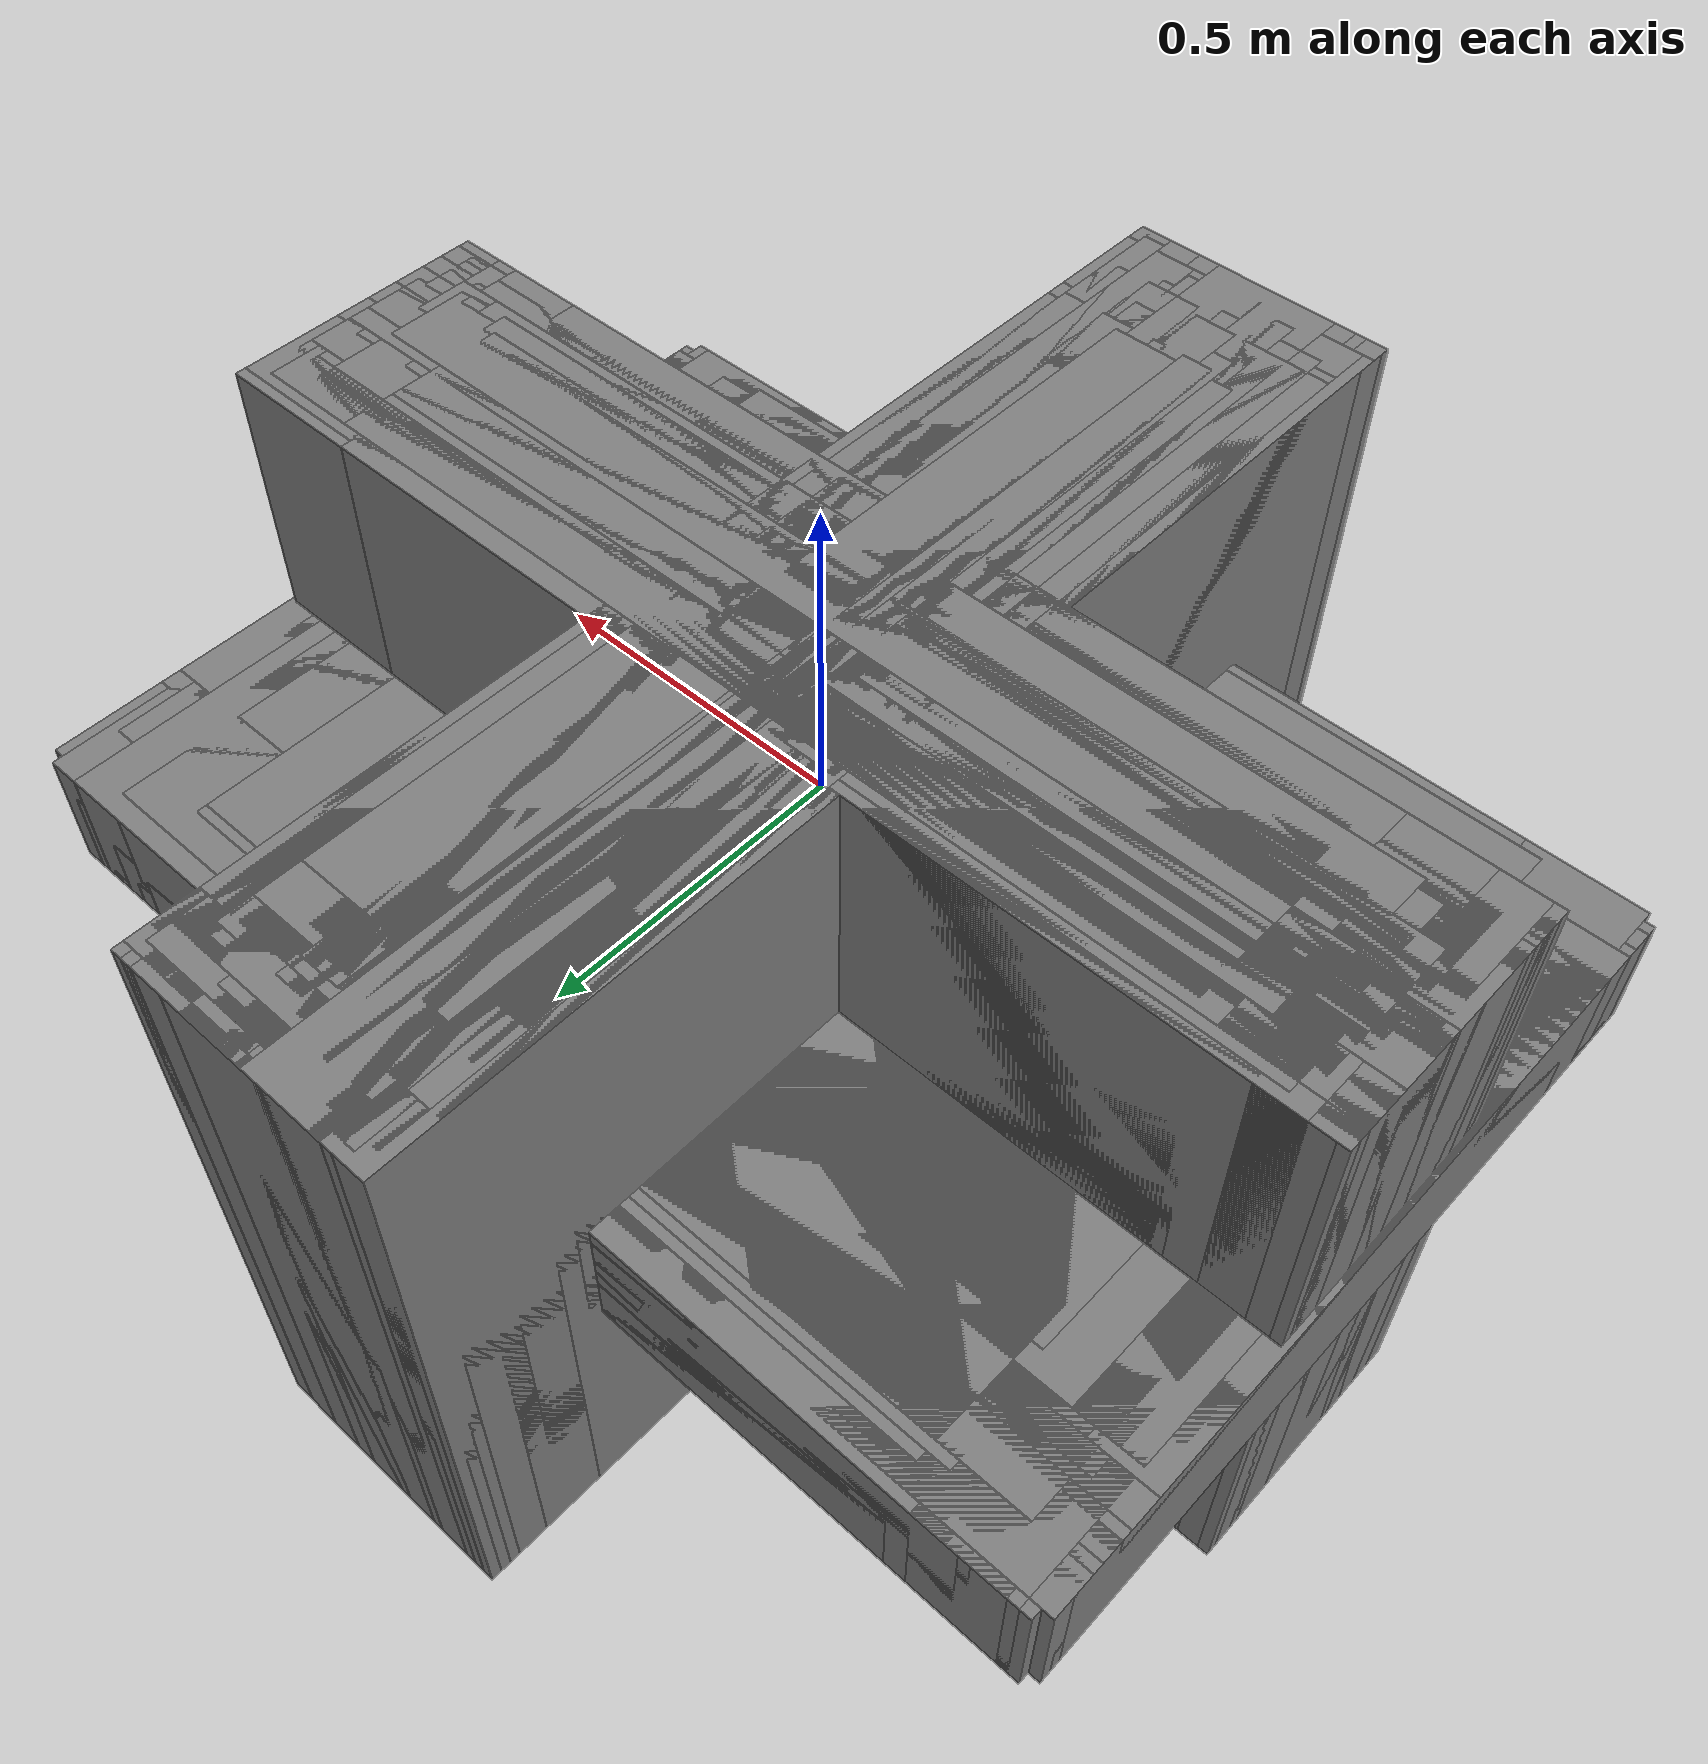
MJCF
<mujoco>
    <asset>
        <mesh file="wrecking-ball/link.obj" name="wrecking-ball/link"/>
    </asset>
    <worldbody>
        <body pos="-0.0165 0.0 0" quat="-2.16489e-17 -0.707107 0.707107 2.16489e-17">
            <geom mesh="wrecking-ball/link" type="mesh" size="0.010000 0.010000 0.010000" density="7680.000000"/>
            <inertial mass="0"/>
        </body>
        <body pos="-0.0165 0.008 0" quat="0.707107 -2.16489e-17 -0.707107 -2.16489e-17">
            <geom mesh="wrecking-ball/link" type="mesh" size="0.010000 0.010000 0.010000" density="7680.000000"/>
        </body>
        <body pos="-0.033 0.0 0" quat="-2.16489e-17 -0.707107 0.707107 2.16489e-17">
            <geom mesh="wrecking-ball/link" type="mesh" size="0.010000 0.010000 0.010000" density="7680.000000"/>
            <inertial mass="0"/>
        </body>
        <body pos="-0.033 0.008 0" quat="0.707107 -2.16489e-17 -0.707107 -2.16489e-17">
            <geom mesh="wrecking-ball/link" type="mesh" size="0.010000 0.010000 0.010000" density="7680.000000"/>
        </body>
        <body pos="-0.0495 0.0 0" quat="-2.16489e-17 -0.707107 0.707107 2.16489e-17">
            <geom mesh="wrecking-ball/link" type="mesh" size="0.010000 0.010000 0.010000" density="7680.000000"/>
            <inertial mass="0"/>
        </body>
        <body pos="-0.0495 0.008 0" quat="0.707107 -2.16489e-17 -0.707107 -2.16489e-17">
            <geom mesh="wrecking-ball/link" type="mesh" size="0.010000 0.010000 0.010000" density="7680.000000"/>
        </body>
        <body pos="-0.066 0.0 0" quat="-2.16489e-17 -0.707107 0.707107 2.16489e-17">
            <geom mesh="wrecking-ball/link" type="mesh" size="0.010000 0.010000 0.010000" density="7680.000000"/>
            <inertial mass="0"/>
        </body>
        <body pos="-0.066 0.008 0" quat="0.707107 -2.16489e-17 -0.707107 -2.16489e-17">
            <geom mesh="wrecking-ball/link" type="mesh" size="0.010000 0.010000 0.010000" density="7680.000000"/>
        </body>
        <body pos="-0.0825 0.0 0" quat="-2.16489e-17 -0.707107 0.707107 2.16489e-17">
            <geom mesh="wrecking-ball/link" type="mesh" size="0.010000 0.010000 0.010000" density="7680.000000"/>
            <inertial mass="0"/>
        </body>
        <body pos="-0.0825 0.008 0" quat="0.707107 -2.16489e-17 -0.707107 -2.16489e-17">
            <geom mesh="wrecking-ball/link" type="mesh" size="0.010000 0.010000 0.010000" density="7680.000000"/>
        </body>
        <body pos="-0.099 0.0 0" quat="-2.16489e-17 -0.707107 0.707107 2.16489e-17">
            <geom mesh="wrecking-ball/link" type="mesh" size="0.010000 0.010000 0.010000" density="7680.000000"/>
            <inertial mass="0"/>
        </body>
        <body pos="-0.099 0.008 0" quat="0.707107 -2.16489e-17 -0.707107 -2.16489e-17">
            <geom mesh="wrecking-ball/link" type="mesh" size="0.010000 0.010000 0.010000" density="7680.000000"/>
        </body>
        <body pos="-0.1155 0.0 0" quat="-2.16489e-17 -0.707107 0.707107 2.16489e-17">
            <geom mesh="wrecking-ball/link" type="mesh" size="0.010000 0.010000 0.010000" density="7680.000000"/>
            <inertial mass="0"/>
        </body>
        <body pos="-0.1155 0.008 0" quat="0.707107 -2.16489e-17 -0.707107 -2.16489e-17">
            <geom mesh="wrecking-ball/link" type="mesh" size="0.010000 0.010000 0.010000" density="7680.000000"/>
        </body>
        <body pos="-0.132 0.0 0" quat="-2.16489e-17 -0.707107 0.707107 2.16489e-17">
            <geom mesh="wrecking-ball/link" type="mesh" size="0.010000 0.010000 0.010000" density="7680.000000"/>
            <inertial mass="0"/>
        </body>
        <body pos="-0.132 0.008 0" quat="0.707107 -2.16489e-17 -0.707107 -2.16489e-17">
            <geom mesh="wrecking-ball/link" type="mesh" size="0.010000 0.010000 0.010000" density="7680.000000"/>
        </body>
        <body pos="-0.1485 0.0 0" quat="-2.16489e-17 -0.707107 0.707107 2.16489e-17">
            <geom mesh="wrecking-ball/link" type="mesh" size="0.010000 0.010000 0.010000" density="7680.000000"/>
            <inertial mass="0"/>
        </body>
        <body pos="-0.1485 0.008 0" quat="0.707107 -2.16489e-17 -0.707107 -2.16489e-17">
            <geom mesh="wrecking-ball/link" type="mesh" size="0.010000 0.010000 0.010000" density="7680.000000"/>
        </body>
        <body pos="-0.165 0.0 0" quat="-2.16489e-17 -0.707107 0.707107 2.16489e-17">
            <geom mesh="wrecking-ball/link" type="mesh" size="0.010000 0.010000 0.010000" density="7680.000000"/>
            <inertial mass="0"/>
        </body>
        <body pos="-0.165 0.008 0" quat="0.707107 -2.16489e-17 -0.707107 -2.16489e-17">
            <geom mesh="wrecking-ball/link" type="mesh" size="0.010000 0.010000 0.010000" density="7680.000000"/>
        </body>
        <body pos="-0.1815 0.0 0" quat="-2.16489e-17 -0.707107 0.707107 2.16489e-17">
            <geom mesh="wrecking-ball/link" type="mesh" size="0.010000 0.010000 0.010000" density="7680.000000"/>
            <inertial mass="0"/>
        </body>
        <body pos="-0.1815 0.008 0" quat="0.707107 -2.16489e-17 -0.707107 -2.16489e-17">
            <geom mesh="wrecking-ball/link" type="mesh" size="0.010000 0.010000 0.010000" density="7680.000000"/>
        </body>
        <body pos="-0.198 0.0 0" quat="-2.16489e-17 -0.707107 0.707107 2.16489e-17">
            <geom mesh="wrecking-ball/link" type="mesh" size="0.010000 0.010000 0.010000" density="7680.000000"/>
            <inertial mass="0"/>
        </body>
        <body pos="-0.198 0.008 0" quat="0.707107 -2.16489e-17 -0.707107 -2.16489e-17">
            <geom mesh="wrecking-ball/link" type="mesh" size="0.010000 0.010000 0.010000" density="7680.000000"/>
        </body>
        <body pos="-0.2145 0.0 0" quat="-2.16489e-17 -0.707107 0.707107 2.16489e-17">
            <geom mesh="wrecking-ball/link" type="mesh" size="0.010000 0.010000 0.010000" density="7680.000000"/>
            <inertial mass="0"/>
        </body>
        <body pos="-0.2145 0.008 0" quat="0.707107 -2.16489e-17 -0.707107 -2.16489e-17">
            <geom mesh="wrecking-ball/link" type="mesh" size="0.010000 0.010000 0.010000" density="7680.000000"/>
        </body>
        <body pos="-0.231 0.0 0" quat="-2.16489e-17 -0.707107 0.707107 2.16489e-17">
            <geom mesh="wrecking-ball/link" type="mesh" size="0.010000 0.010000 0.010000" density="7680.000000"/>
            <inertial mass="0"/>
        </body>
        <body pos="-0.231 0.008 0" quat="0.707107 -2.16489e-17 -0.707107 -2.16489e-17">
            <geom mesh="wrecking-ball/link" type="mesh" size="0.010000 0.010000 0.010000" density="7680.000000"/>
        </body>
        <body pos="-0 0.016 0" quat="-2.16489e-17 -0.707107 0.707107 2.16489e-17">
            <geom mesh="wrecking-ball/link" type="mesh" size="0.010000 0.010000 0.010000" density="7680.000000"/>
            <inertial mass="0"/>
        </body>
        <body pos="-0.00825 0.016 0" quat="-0.5 0.5 0.5 0.5">
            <geom mesh="wrecking-ball/link" type="mesh" size="0.010000 0.010000 0.010000" density="7680.000000"/>
        </body>
        <body pos="-0.0165 0.016 0" quat="-2.16489e-17 -0.707107 0.707107 2.16489e-17">
            <geom mesh="wrecking-ball/link" type="mesh" size="0.010000 0.010000 0.010000" density="7680.000000"/>
        </body>
        <body pos="-0.02475 0.016 0" quat="-0.5 0.5 0.5 0.5">
            <geom mesh="wrecking-ball/link" type="mesh" size="0.010000 0.010000 0.010000" density="7680.000000"/>
        </body>
        <body pos="-0.0165 0.024 0" quat="0.707107 -2.16489e-17 -0.707107 -2.16489e-17">
            <geom mesh="wrecking-ball/link" type="mesh" size="0.010000 0.010000 0.010000" density="7680.000000"/>
        </body>
        <body pos="-0.033 0.016 0" quat="-2.16489e-17 -0.707107 0.707107 2.16489e-17">
            <geom mesh="wrecking-ball/link" type="mesh" size="0.010000 0.010000 0.010000" density="7680.000000"/>
        </body>
        <body pos="-0.04125 0.016 0" quat="-0.5 0.5 0.5 0.5">
            <geom mesh="wrecking-ball/link" type="mesh" size="0.010000 0.010000 0.010000" density="7680.000000"/>
        </body>
        <body pos="-0.033 0.024 0" quat="0.707107 -2.16489e-17 -0.707107 -2.16489e-17">
            <geom mesh="wrecking-ball/link" type="mesh" size="0.010000 0.010000 0.010000" density="7680.000000"/>
        </body>
        <body pos="-0.0495 0.016 0" quat="-2.16489e-17 -0.707107 0.707107 2.16489e-17">
            <geom mesh="wrecking-ball/link" type="mesh" size="0.010000 0.010000 0.010000" density="7680.000000"/>
        </body>
        <body pos="-0.05775 0.016 0" quat="-0.5 0.5 0.5 0.5">
            <geom mesh="wrecking-ball/link" type="mesh" size="0.010000 0.010000 0.010000" density="7680.000000"/>
        </body>
        <body pos="-0.0495 0.024 0" quat="0.707107 -2.16489e-17 -0.707107 -2.16489e-17">
            <geom mesh="wrecking-ball/link" type="mesh" size="0.010000 0.010000 0.010000" density="7680.000000"/>
        </body>
        <body pos="-0.066 0.016 0" quat="-2.16489e-17 -0.707107 0.707107 2.16489e-17">
            <geom mesh="wrecking-ball/link" type="mesh" size="0.010000 0.010000 0.010000" density="7680.000000"/>
        </body>
        <body pos="-0.07425 0.016 0" quat="-0.5 0.5 0.5 0.5">
            <geom mesh="wrecking-ball/link" type="mesh" size="0.010000 0.010000 0.010000" density="7680.000000"/>
        </body>
        <body pos="-0.066 0.024 0" quat="0.707107 -2.16489e-17 -0.707107 -2.16489e-17">
            <geom mesh="wrecking-ball/link" type="mesh" size="0.010000 0.010000 0.010000" density="7680.000000"/>
        </body>
        <body pos="-0.0825 0.016 0" quat="-2.16489e-17 -0.707107 0.707107 2.16489e-17">
            <geom mesh="wrecking-ball/link" type="mesh" size="0.010000 0.010000 0.010000" density="7680.000000"/>
        </body>
        <body pos="-0.09075 0.016 0" quat="-0.5 0.5 0.5 0.5">
            <geom mesh="wrecking-ball/link" type="mesh" size="0.010000 0.010000 0.010000" density="7680.000000"/>
        </body>
        <body pos="-0.0825 0.024 0" quat="0.707107 -2.16489e-17 -0.707107 -2.16489e-17">
            <geom mesh="wrecking-ball/link" type="mesh" size="0.010000 0.010000 0.010000" density="7680.000000"/>
        </body>
        <body pos="-0.099 0.016 0" quat="-2.16489e-17 -0.707107 0.707107 2.16489e-17">
            <geom mesh="wrecking-ball/link" type="mesh" size="0.010000 0.010000 0.010000" density="7680.000000"/>
        </body>
        <body pos="-0.10725 0.016 0" quat="-0.5 0.5 0.5 0.5">
            <geom mesh="wrecking-ball/link" type="mesh" size="0.010000 0.010000 0.010000" density="7680.000000"/>
        </body>
        <body pos="-0.099 0.024 0" quat="0.707107 -2.16489e-17 -0.707107 -2.16489e-17">
            <geom mesh="wrecking-ball/link" type="mesh" size="0.010000 0.010000 0.010000" density="7680.000000"/>
        </body>
        <body pos="-0.1155 0.016 0" quat="-2.16489e-17 -0.707107 0.707107 2.16489e-17">
            <geom mesh="wrecking-ball/link" type="mesh" size="0.010000 0.010000 0.010000" density="7680.000000"/>
        </body>
        <body pos="-0.12375 0.016 0" quat="-0.5 0.5 0.5 0.5">
            <geom mesh="wrecking-ball/link" type="mesh" size="0.010000 0.010000 0.010000" density="7680.000000"/>
        </body>
        <body pos="-0.1155 0.024 0" quat="0.707107 -2.16489e-17 -0.707107 -2.16489e-17">
            <geom mesh="wrecking-ball/link" type="mesh" size="0.010000 0.010000 0.010000" density="7680.000000"/>
        </body>
        <body pos="-0.132 0.016 0" quat="-2.16489e-17 -0.707107 0.707107 2.16489e-17">
            <geom mesh="wrecking-ball/link" type="mesh" size="0.010000 0.010000 0.010000" density="7680.000000"/>
        </body>
        <body pos="-0.14025 0.016 0" quat="-0.5 0.5 0.5 0.5">
            <geom mesh="wrecking-ball/link" type="mesh" size="0.010000 0.010000 0.010000" density="7680.000000"/>
        </body>
        <body pos="-0.132 0.024 0" quat="0.707107 -2.16489e-17 -0.707107 -2.16489e-17">
            <geom mesh="wrecking-ball/link" type="mesh" size="0.010000 0.010000 0.010000" density="7680.000000"/>
        </body>
        <body pos="-0.1485 0.016 0" quat="-2.16489e-17 -0.707107 0.707107 2.16489e-17">
            <geom mesh="wrecking-ball/link" type="mesh" size="0.010000 0.010000 0.010000" density="7680.000000"/>
        </body>
        <body pos="-0.15675 0.016 0" quat="-0.5 0.5 0.5 0.5">
            <geom mesh="wrecking-ball/link" type="mesh" size="0.010000 0.010000 0.010000" density="7680.000000"/>
        </body>
        <body pos="-0.1485 0.024 0" quat="0.707107 -2.16489e-17 -0.707107 -2.16489e-17">
            <geom mesh="wrecking-ball/link" type="mesh" size="0.010000 0.010000 0.010000" density="7680.000000"/>
        </body>
        <body pos="-0.165 0.016 0" quat="-2.16489e-17 -0.707107 0.707107 2.16489e-17">
            <geom mesh="wrecking-ball/link" type="mesh" size="0.010000 0.010000 0.010000" density="7680.000000"/>
        </body>
        <body pos="-0.17325 0.016 0" quat="-0.5 0.5 0.5 0.5">
            <geom mesh="wrecking-ball/link" type="mesh" size="0.010000 0.010000 0.010000" density="7680.000000"/>
        </body>
        <body pos="-0.165 0.024 0" quat="0.707107 -2.16489e-17 -0.707107 -2.16489e-17">
            <geom mesh="wrecking-ball/link" type="mesh" size="0.010000 0.010000 0.010000" density="7680.000000"/>
        </body>
        <body pos="-0.1815 0.016 0" quat="-2.16489e-17 -0.707107 0.707107 2.16489e-17">
            <geom mesh="wrecking-ball/link" type="mesh" size="0.010000 0.010000 0.010000" density="7680.000000"/>
        </body>
        <body pos="-0.18975 0.016 0" quat="-0.5 0.5 0.5 0.5">
            <geom mesh="wrecking-ball/link" type="mesh" size="0.010000 0.010000 0.010000" density="7680.000000"/>
        </body>
        <body pos="-0.1815 0.024 0" quat="0.707107 -2.16489e-17 -0.707107 -2.16489e-17">
            <geom mesh="wrecking-ball/link" type="mesh" size="0.010000 0.010000 0.010000" density="7680.000000"/>
        </body>
        <body pos="-0.198 0.016 0" quat="-2.16489e-17 -0.707107 0.707107 2.16489e-17">
            <geom mesh="wrecking-ball/link" type="mesh" size="0.010000 0.010000 0.010000" density="7680.000000"/>
        </body>
        <body pos="-0.20625 0.016 0" quat="-0.5 0.5 0.5 0.5">
            <geom mesh="wrecking-ball/link" type="mesh" size="0.010000 0.010000 0.010000" density="7680.000000"/>
        </body>
        <body pos="-0.198 0.024 0" quat="0.707107 -2.16489e-17 -0.707107 -2.16489e-17">
            <geom mesh="wrecking-ball/link" type="mesh" size="0.010000 0.010000 0.010000" density="7680.000000"/>
        </body>
        <body pos="-0.2145 0.016 0" quat="-2.16489e-17 -0.707107 0.707107 2.16489e-17">
            <geom mesh="wrecking-ball/link" type="mesh" size="0.010000 0.010000 0.010000" density="7680.000000"/>
        </body>
        <body pos="-0.22275 0.016 0" quat="-0.5 0.5 0.5 0.5">
            <geom mesh="wrecking-ball/link" type="mesh" size="0.010000 0.010000 0.010000" density="7680.000000"/>
        </body>
        <body pos="-0.2145 0.024 0" quat="0.707107 -2.16489e-17 -0.707107 -2.16489e-17">
            <geom mesh="wrecking-ball/link" type="mesh" size="0.010000 0.010000 0.010000" density="7680.000000"/>
        </body>
        <body pos="-0.231 0.016 0" quat="-2.16489e-17 -0.707107 0.707107 2.16489e-17">
            <geom mesh="wrecking-ball/link" type="mesh" size="0.010000 0.010000 0.010000" density="7680.000000"/>
        </body>
        <body pos="-0.23925 0.016 0" quat="-0.5 0.5 0.5 0.5">
            <geom mesh="wrecking-ball/link" type="mesh" size="0.010000 0.010000 0.010000" density="7680.000000"/>
        </body>
        <body pos="-0.231 0.024 0" quat="0.707107 -2.16489e-17 -0.707107 -2.16489e-17">
            <geom mesh="wrecking-ball/link" type="mesh" size="0.010000 0.010000 0.010000" density="7680.000000"/>
        </body>
        <body pos="-0.2475 0.016 0" quat="-2.16489e-17 -0.707107 0.707107 2.16489e-17">
            <geom mesh="wrecking-ball/link" type="mesh" size="0.010000 0.010000 0.010000" density="7680.000000"/>
            <inertial mass="0"/>
        </body>
        <body pos="-0 0.032 0" quat="-2.16489e-17 -0.707107 0.707107 2.16489e-17">
            <geom mesh="wrecking-ball/link" type="mesh" size="0.010000 0.010000 0.010000" density="7680.000000"/>
            <inertial mass="0"/>
        </body>
        <body pos="-0.00825 0.032 0" quat="-0.5 0.5 0.5 0.5">
            <geom mesh="wrecking-ball/link" type="mesh" size="0.010000 0.010000 0.010000" density="7680.000000"/>
        </body>
        <body pos="-0.0165 0.032 0" quat="-2.16489e-17 -0.707107 0.707107 2.16489e-17">
            <geom mesh="wrecking-ball/link" type="mesh" size="0.010000 0.010000 0.010000" density="7680.000000"/>
        </body>
        <body pos="-0.02475 0.032 0" quat="-0.5 0.5 0.5 0.5">
            <geom mesh="wrecking-ball/link" type="mesh" size="0.010000 0.010000 0.010000" density="7680.000000"/>
        </body>
        <body pos="-0.0165 0.04 0" quat="0.707107 -2.16489e-17 -0.707107 -2.16489e-17">
            <geom mesh="wrecking-ball/link" type="mesh" size="0.010000 0.010000 0.010000" density="7680.000000"/>
        </body>
        <body pos="-0.033 0.032 0" quat="-2.16489e-17 -0.707107 0.707107 2.16489e-17">
            <geom mesh="wrecking-ball/link" type="mesh" size="0.010000 0.010000 0.010000" density="7680.000000"/>
        </body>
        <body pos="-0.04125 0.032 0" quat="-0.5 0.5 0.5 0.5">
            <geom mesh="wrecking-ball/link" type="mesh" size="0.010000 0.010000 0.010000" density="7680.000000"/>
        </body>
        <body pos="-0.033 0.04 0" quat="0.707107 -2.16489e-17 -0.707107 -2.16489e-17">
            <geom mesh="wrecking-ball/link" type="mesh" size="0.010000 0.010000 0.010000" density="7680.000000"/>
        </body>
        <body pos="-0.0495 0.032 0" quat="-2.16489e-17 -0.707107 0.707107 2.16489e-17">
            <geom mesh="wrecking-ball/link" type="mesh" size="0.010000 0.010000 0.010000" density="7680.000000"/>
        </body>
        <body pos="-0.05775 0.032 0" quat="-0.5 0.5 0.5 0.5">
            <geom mesh="wrecking-ball/link" type="mesh" size="0.010000 0.010000 0.010000" density="7680.000000"/>
        </body>
        <body pos="-0.0495 0.04 0" quat="0.707107 -2.16489e-17 -0.707107 -2.16489e-17">
            <geom mesh="wrecking-ball/link" type="mesh" size="0.010000 0.010000 0.010000" density="7680.000000"/>
        </body>
        <body pos="-0.066 0.032 0" quat="-2.16489e-17 -0.707107 0.707107 2.16489e-17">
            <geom mesh="wrecking-ball/link" type="mesh" size="0.010000 0.010000 0.010000" density="7680.000000"/>
        </body>
        <body pos="-0.07425 0.032 0" quat="-0.5 0.5 0.5 0.5">
            <geom mesh="wrecking-ball/link" type="mesh" size="0.010000 0.010000 0.010000" density="7680.000000"/>
        </body>
        <body pos="-0.066 0.04 0" quat="0.707107 -2.16489e-17 -0.707107 -2.16489e-17">
            <geom mesh="wrecking-ball/link" type="mesh" size="0.010000 0.010000 0.010000" density="7680.000000"/>
        </body>
        <body pos="-0.0825 0.032 0" quat="-2.16489e-17 -0.707107 0.707107 2.16489e-17">
            <geom mesh="wrecking-ball/link" type="mesh" size="0.010000 0.010000 0.010000" density="7680.000000"/>
        </body>
        <body pos="-0.09075 0.032 0" quat="-0.5 0.5 0.5 0.5">
            <geom mesh="wrecking-ball/link" type="mesh" size="0.010000 0.010000 0.010000" density="7680.000000"/>
        </body>
        <body pos="-0.0825 0.04 0" quat="0.707107 -2.16489e-17 -0.707107 -2.16489e-17">
            <geom mesh="wrecking-ball/link" type="mesh" size="0.010000 0.010000 0.010000" density="7680.000000"/>
        </body>
        <body pos="-0.099 0.032 0" quat="-2.16489e-17 -0.707107 0.707107 2.16489e-17">
            <geom mesh="wrecking-ball/link" type="mesh" size="0.010000 0.010000 0.010000" density="7680.000000"/>
        </body>
        <body pos="-0.10725 0.032 0" quat="-0.5 0.5 0.5 0.5">
            <geom mesh="wrecking-ball/link" type="mesh" size="0.010000 0.010000 0.010000" density="7680.000000"/>
        </body>
        <body pos="-0.099 0.04 0" quat="0.707107 -2.16489e-17 -0.707107 -2.16489e-17">
            <geom mesh="wrecking-ball/link" type="mesh" size="0.010000 0.010000 0.010000" density="7680.000000"/>
        </body>
        <body pos="-0.1155 0.032 0" quat="-2.16489e-17 -0.707107 0.707107 2.16489e-17">
            <geom mesh="wrecking-ball/link" type="mesh" size="0.010000 0.010000 0.010000" density="7680.000000"/>
        </body>
        <body pos="-0.12375 0.032 0" quat="-0.5 0.5 0.5 0.5">
            <geom mesh="wrecking-ball/link" type="mesh" size="0.010000 0.010000 0.010000" density="7680.000000"/>
        </body>
        <body pos="-0.1155 0.04 0" quat="0.707107 -2.16489e-17 -0.707107 -2.16489e-17">
            <geom mesh="wrecking-ball/link" type="mesh" size="0.010000 0.010000 0.010000" density="7680.000000"/>
        </body>
        <body pos="-0.132 0.032 0" quat="-2.16489e-17 -0.707107 0.707107 2.16489e-17">
            <geom mesh="wrecking-ball/link" type="mesh" size="0.010000 0.010000 0.010000" density="7680.000000"/>
        </body>
        <body pos="-0.14025 0.032 0" quat="-0.5 0.5 0.5 0.5">
            <geom mesh="wrecking-ball/link" type="mesh" size="0.010000 0.010000 0.010000" density="7680.000000"/>
        </body>
        <body pos="-0.132 0.04 0" quat="0.707107 -2.16489e-17 -0.707107 -2.16489e-17">
            <geom mesh="wrecking-ball/link" type="mesh" size="0.010000 0.010000 0.010000" density="7680.000000"/>
        </body>
        <body pos="-0.1485 0.032 0" quat="-2.16489e-17 -0.707107 0.707107 2.16489e-17">
            <geom mesh="wrecking-ball/link" type="mesh" size="0.010000 0.010000 0.010000" density="7680.000000"/>
        </body>
        <body pos="-0.15675 0.032 0" quat="-0.5 0.5 0.5 0.5">
            <geom mesh="wrecking-ball/link" type="mesh" size="0.010000 0.010000 0.010000" density="7680.000000"/>
        </body>
        <body pos="-0.1485 0.04 0" quat="0.707107 -2.16489e-17 -0.707107 -2.16489e-17">
            <geom mesh="wrecking-ball/link" type="mesh" size="0.010000 0.010000 0.010000" density="7680.000000"/>
        </body>
        <body pos="-0.165 0.032 0" quat="-2.16489e-17 -0.707107 0.707107 2.16489e-17">
            <geom mesh="wrecking-ball/link" type="mesh" size="0.010000 0.010000 0.010000" density="7680.000000"/>
        </body>
        <body pos="-0.17325 0.032 0" quat="-0.5 0.5 0.5 0.5">
            <geom mesh="wrecking-ball/link" type="mesh" size="0.010000 0.010000 0.010000" density="7680.000000"/>
        </body>
        <body pos="-0.165 0.04 0" quat="0.707107 -2.16489e-17 -0.707107 -2.16489e-17">
            <geom mesh="wrecking-ball/link" type="mesh" size="0.010000 0.010000 0.010000" density="7680.000000"/>
        </body>
        <body pos="-0.1815 0.032 0" quat="-2.16489e-17 -0.707107 0.707107 2.16489e-17">
            <geom mesh="wrecking-ball/link" type="mesh" size="0.010000 0.010000 0.010000" density="7680.000000"/>
        </body>
        <body pos="-0.18975 0.032 0" quat="-0.5 0.5 0.5 0.5">
            <geom mesh="wrecking-ball/link" type="mesh" size="0.010000 0.010000 0.010000" density="7680.000000"/>
        </body>
        <body pos="-0.1815 0.04 0" quat="0.707107 -2.16489e-17 -0.707107 -2.16489e-17">
            <geom mesh="wrecking-ball/link" type="mesh" size="0.010000 0.010000 0.010000" density="7680.000000"/>
        </body>
        <body pos="-0.198 0.032 0" quat="-2.16489e-17 -0.707107 0.707107 2.16489e-17">
            <geom mesh="wrecking-ball/link" type="mesh" size="0.010000 0.010000 0.010000" density="7680.000000"/>
        </body>
        <body pos="-0.20625 0.032 0" quat="-0.5 0.5 0.5 0.5">
            <geom mesh="wrecking-ball/link" type="mesh" size="0.010000 0.010000 0.010000" density="7680.000000"/>
        </body>
        <body pos="-0.198 0.04 0" quat="0.707107 -2.16489e-17 -0.707107 -2.16489e-17">
            <geom mesh="wrecking-ball/link" type="mesh" size="0.010000 0.010000 0.010000" density="7680.000000"/>
        </body>
        <body pos="-0.2145 0.032 0" quat="-2.16489e-17 -0.707107 0.707107 2.16489e-17">
            <geom mesh="wrecking-ball/link" type="mesh" size="0.010000 0.010000 0.010000" density="7680.000000"/>
        </body>
        <body pos="-0.22275 0.032 0" quat="-0.5 0.5 0.5 0.5">
            <geom mesh="wrecking-ball/link" type="mesh" size="0.010000 0.010000 0.010000" density="7680.000000"/>
        </body>
        <body pos="-0.2145 0.04 0" quat="0.707107 -2.16489e-17 -0.707107 -2.16489e-17">
            <geom mesh="wrecking-ball/link" type="mesh" size="0.010000 0.010000 0.010000" density="7680.000000"/>
        </body>
        <body pos="-0.231 0.032 0" quat="-2.16489e-17 -0.707107 0.707107 2.16489e-17">
            <geom mesh="wrecking-ball/link" type="mesh" size="0.010000 0.010000 0.010000" density="7680.000000"/>
        </body>
        <body pos="-0.23925 0.032 0" quat="-0.5 0.5 0.5 0.5">
            <geom mesh="wrecking-ball/link" type="mesh" size="0.010000 0.010000 0.010000" density="7680.000000"/>
        </body>
        <body pos="-0.231 0.04 0" quat="0.707107 -2.16489e-17 -0.707107 -2.16489e-17">
            <geom mesh="wrecking-ball/link" type="mesh" size="0.010000 0.010000 0.010000" density="7680.000000"/>
        </body>
        <body pos="-0.2475 0.032 0" quat="-2.16489e-17 -0.707107 0.707107 2.16489e-17">
            <geom mesh="wrecking-ball/link" type="mesh" size="0.010000 0.010000 0.010000" density="7680.000000"/>
            <inertial mass="0"/>
        </body>
        <body pos="-0 0.048 0" quat="-2.16489e-17 -0.707107 0.707107 2.16489e-17">
            <geom mesh="wrecking-ball/link" type="mesh" size="0.010000 0.010000 0.010000" density="7680.000000"/>
            <inertial mass="0"/>
        </body>
        <body pos="-0.00825 0.048 0" quat="-0.5 0.5 0.5 0.5">
            <geom mesh="wrecking-ball/link" type="mesh" size="0.010000 0.010000 0.010000" density="7680.000000"/>
        </body>
        <body pos="-0.0165 0.048 0" quat="-2.16489e-17 -0.707107 0.707107 2.16489e-17">
            <geom mesh="wrecking-ball/link" type="mesh" size="0.010000 0.010000 0.010000" density="7680.000000"/>
        </body>
        <body pos="-0.02475 0.048 0" quat="-0.5 0.5 0.5 0.5">
            <geom mesh="wrecking-ball/link" type="mesh" size="0.010000 0.010000 0.010000" density="7680.000000"/>
        </body>
        <body pos="-0.0165 0.056 0" quat="0.707107 -2.16489e-17 -0.707107 -2.16489e-17">
            <geom mesh="wrecking-ball/link" type="mesh" size="0.010000 0.010000 0.010000" density="7680.000000"/>
        </body>
        <body pos="-0.033 0.048 0" quat="-2.16489e-17 -0.707107 0.707107 2.16489e-17">
            <geom mesh="wrecking-ball/link" type="mesh" size="0.010000 0.010000 0.010000" density="7680.000000"/>
        </body>
        <body pos="-0.04125 0.048 0" quat="-0.5 0.5 0.5 0.5">
            <geom mesh="wrecking-ball/link" type="mesh" size="0.010000 0.010000 0.010000" density="7680.000000"/>
        </body>
        <body pos="-0.033 0.056 0" quat="0.707107 -2.16489e-17 -0.707107 -2.16489e-17">
            <geom mesh="wrecking-ball/link" type="mesh" size="0.010000 0.010000 0.010000" density="7680.000000"/>
        </body>
        <body pos="-0.0495 0.048 0" quat="-2.16489e-17 -0.707107 0.707107 2.16489e-17">
            <geom mesh="wrecking-ball/link" type="mesh" size="0.010000 0.010000 0.010000" density="7680.000000"/>
        </body>
        <body pos="-0.05775 0.048 0" quat="-0.5 0.5 0.5 0.5">
            <geom mesh="wrecking-ball/link" type="mesh" size="0.010000 0.010000 0.010000" density="7680.000000"/>
        </body>
        <body pos="-0.0495 0.056 0" quat="0.707107 -2.16489e-17 -0.707107 -2.16489e-17">
            <geom mesh="wrecking-ball/link" type="mesh" size="0.010000 0.010000 0.010000" density="7680.000000"/>
        </body>
        <body pos="-0.066 0.048 0" quat="-2.16489e-17 -0.707107 0.707107 2.16489e-17">
            <geom mesh="wrecking-ball/link" type="mesh" size="0.010000 0.010000 0.010000" density="7680.000000"/>
        </body>
        <body pos="-0.07425 0.048 0" quat="-0.5 0.5 0.5 0.5">
            <geom mesh="wrecking-ball/link" type="mesh" size="0.010000 0.010000 0.010000" density="7680.000000"/>
        </body>
        <body pos="-0.066 0.056 0" quat="0.707107 -2.16489e-17 -0.707107 -2.16489e-17">
            <geom mesh="wrecking-ball/link" type="mesh" size="0.010000 0.010000 0.010000" density="7680.000000"/>
        </body>
        <body pos="-0.0825 0.048 0" quat="-2.16489e-17 -0.707107 0.707107 2.16489e-17">
            <geom mesh="wrecking-ball/link" type="mesh" size="0.010000 0.010000 0.010000" density="7680.000000"/>
        </body>
        <body pos="-0.09075 0.048 0" quat="-0.5 0.5 0.5 0.5">
            <geom mesh="wrecking-ball/link" type="mesh" size="0.010000 0.010000 0.010000" density="7680.000000"/>
        </body>
        <body pos="-0.0825 0.056 0" quat="0.707107 -2.16489e-17 -0.707107 -2.16489e-17">
            <geom mesh="wrecking-ball/link" type="mesh" size="0.010000 0.010000 0.010000" density="7680.000000"/>
        </body>
        <body pos="-0.099 0.048 0" quat="-2.16489e-17 -0.707107 0.707107 2.16489e-17">
            <geom mesh="wrecking-ball/link" type="mesh" size="0.010000 0.010000 0.010000" density="7680.000000"/>
        </body>
        <body pos="-0.10725 0.048 0" quat="-0.5 0.5 0.5 0.5">
            <geom mesh="wrecking-ball/link" type="mesh" size="0.010000 0.010000 0.010000" density="7680.000000"/>
        </body>
        <body pos="-0.099 0.056 0" quat="0.707107 -2.16489e-17 -0.707107 -2.16489e-17">
            <geom mesh="wrecking-ball/link" type="mesh" size="0.010000 0.010000 0.010000" density="7680.000000"/>
        </body>
        <body pos="-0.1155 0.048 0" quat="-2.16489e-17 -0.707107 0.707107 2.16489e-17">
            <geom mesh="wrecking-ball/link" type="mesh" size="0.010000 0.010000 0.010000" density="7680.000000"/>
        </body>
        <body pos="-0.12375 0.048 0" quat="-0.5 0.5 0.5 0.5">
            <geom mesh="wrecking-ball/link" type="mesh" size="0.010000 0.010000 0.010000" density="7680.000000"/>
        </body>
        <body pos="-0.1155 0.056 0" quat="0.707107 -2.16489e-17 -0.707107 -2.16489e-17">
            <geom mesh="wrecking-ball/link" type="mesh" size="0.010000 0.010000 0.010000" density="7680.000000"/>
        </body>
        <body pos="-0.132 0.048 0" quat="-2.16489e-17 -0.707107 0.707107 2.16489e-17">
            <geom mesh="wrecking-ball/link" type="mesh" size="0.010000 0.010000 0.010000" density="7680.000000"/>
        </body>
        <body pos="-0.14025 0.048 0" quat="-0.5 0.5 0.5 0.5">
            <geom mesh="wrecking-ball/link" type="mesh" size="0.010000 0.010000 0.010000" density="7680.000000"/>
        </body>
        <body pos="-0.132 0.056 0" quat="0.707107 -2.16489e-17 -0.707107 -2.16489e-17">
            <geom mesh="wrecking-ball/link" type="mesh" size="0.010000 0.010000 0.010000" density="7680.000000"/>
        </body>
        <body pos="-0.1485 0.048 0" quat="-2.16489e-17 -0.707107 0.707107 2.16489e-17">
            <geom mesh="wrecking-ball/link" type="mesh" size="0.010000 0.010000 0.010000" density="7680.000000"/>
        </body>
        <body pos="-0.15675 0.048 0" quat="-0.5 0.5 0.5 0.5">
            <geom mesh="wrecking-ball/link" type="mesh" size="0.010000 0.010000 0.010000" density="7680.000000"/>
        </body>
        <body pos="-0.1485 0.056 0" quat="0.707107 -2.16489e-17 -0.707107 -2.16489e-17">
            <geom mesh="wrecking-ball/link" type="mesh" size="0.010000 0.010000 0.010000" density="7680.000000"/>
        </body>
        <body pos="-0.165 0.048 0" quat="-2.16489e-17 -0.707107 0.707107 2.16489e-17">
            <geom mesh="wrecking-ball/link" type="mesh" size="0.010000 0.010000 0.010000" density="7680.000000"/>
        </body>
        <body pos="-0.17325 0.048 0" quat="-0.5 0.5 0.5 0.5">
            <geom mesh="wrecking-ball/link" type="mesh" size="0.010000 0.010000 0.010000" density="7680.000000"/>
        </body>
        <body pos="-0.165 0.056 0" quat="0.707107 -2.16489e-17 -0.707107 -2.16489e-17">
            <geom mesh="wrecking-ball/link" type="mesh" size="0.010000 0.010000 0.010000" density="7680.000000"/>
        </body>
        <body pos="-0.1815 0.048 0" quat="-2.16489e-17 -0.707107 0.707107 2.16489e-17">
            <geom mesh="wrecking-ball/link" type="mesh" size="0.010000 0.010000 0.010000" density="7680.000000"/>
        </body>
        <body pos="-0.18975 0.048 0" quat="-0.5 0.5 0.5 0.5">
            <geom mesh="wrecking-ball/link" type="mesh" size="0.010000 0.010000 0.010000" density="7680.000000"/>
        </body>
        <body pos="-0.1815 0.056 0" quat="0.707107 -2.16489e-17 -0.707107 -2.16489e-17">
            <geom mesh="wrecking-ball/link" type="mesh" size="0.010000 0.010000 0.010000" density="7680.000000"/>
        </body>
        <body pos="-0.198 0.048 0" quat="-2.16489e-17 -0.707107 0.707107 2.16489e-17">
            <geom mesh="wrecking-ball/link" type="mesh" size="0.010000 0.010000 0.010000" density="7680.000000"/>
        </body>
        <body pos="-0.20625 0.048 0" quat="-0.5 0.5 0.5 0.5">
            <geom mesh="wrecking-ball/link" type="mesh" size="0.010000 0.010000 0.010000" density="7680.000000"/>
        </body>
        <body pos="-0.198 0.056 0" quat="0.707107 -2.16489e-17 -0.707107 -2.16489e-17">
            <geom mesh="wrecking-ball/link" type="mesh" size="0.010000 0.010000 0.010000" density="7680.000000"/>
        </body>
        <body pos="-0.2145 0.048 0" quat="-2.16489e-17 -0.707107 0.707107 2.16489e-17">
            <geom mesh="wrecking-ball/link" type="mesh" size="0.010000 0.010000 0.010000" density="7680.000000"/>
        </body>
        <body pos="-0.22275 0.048 0" quat="-0.5 0.5 0.5 0.5">
            <geom mesh="wrecking-ball/link" type="mesh" size="0.010000 0.010000 0.010000" density="7680.000000"/>
        </body>
        <body pos="-0.2145 0.056 0" quat="0.707107 -2.16489e-17 -0.707107 -2.16489e-17">
            <geom mesh="wrecking-ball/link" type="mesh" size="0.010000 0.010000 0.010000" density="7680.000000"/>
        </body>
        <body pos="-0.231 0.048 0" quat="-2.16489e-17 -0.707107 0.707107 2.16489e-17">
            <geom mesh="wrecking-ball/link" type="mesh" size="0.010000 0.010000 0.010000" density="7680.000000"/>
        </body>
        <body pos="-0.23925 0.048 0" quat="-0.5 0.5 0.5 0.5">
            <geom mesh="wrecking-ball/link" type="mesh" size="0.010000 0.010000 0.010000" density="7680.000000"/>
        </body>
        <body pos="-0.231 0.056 0" quat="0.707107 -2.16489e-17 -0.707107 -2.16489e-17">
            <geom mesh="wrecking-ball/link" type="mesh" size="0.010000 0.010000 0.010000" density="7680.000000"/>
        </body>
        <body pos="-0.2475 0.048 0" quat="-2.16489e-17 -0.707107 0.707107 2.16489e-17">
            <geom mesh="wrecking-ball/link" type="mesh" size="0.010000 0.010000 0.010000" density="7680.000000"/>
            <inertial mass="0"/>
        </body>
        <body pos="-0 0.064 0" quat="-2.16489e-17 -0.707107 0.707107 2.16489e-17">
            <geom mesh="wrecking-ball/link" type="mesh" size="0.010000 0.010000 0.010000" density="7680.000000"/>
            <inertial mass="0"/>
        </body>
        <body pos="-0.00825 0.064 0" quat="-0.5 0.5 0.5 0.5">
            <geom mesh="wrecking-ball/link" type="mesh" size="0.010000 0.010000 0.010000" density="7680.000000"/>
        </body>
        <body pos="-0.0165 0.064 0" quat="-2.16489e-17 -0.707107 0.707107 2.16489e-17">
            <geom mesh="wrecking-ball/link" type="mesh" size="0.010000 0.010000 0.010000" density="7680.000000"/>
        </body>
        <body pos="-0.02475 0.064 0" quat="-0.5 0.5 0.5 0.5">
            <geom mesh="wrecking-ball/link" type="mesh" size="0.010000 0.010000 0.010000" density="7680.000000"/>
        </body>
        <body pos="-0.0165 0.07200000000000001 0" quat="0.707107 -2.16489e-17 -0.707107 -2.16489e-17">
            <geom mesh="wrecking-ball/link" type="mesh" size="0.010000 0.010000 0.010000" density="7680.000000"/>
        </body>
        <body pos="-0.033 0.064 0" quat="-2.16489e-17 -0.707107 0.707107 2.16489e-17">
            <geom mesh="wrecking-ball/link" type="mesh" size="0.010000 0.010000 0.010000" density="7680.000000"/>
        </body>
        <body pos="-0.04125 0.064 0" quat="-0.5 0.5 0.5 0.5">
            <geom mesh="wrecking-ball/link" type="mesh" size="0.010000 0.010000 0.010000" density="7680.000000"/>
        </body>
        <body pos="-0.033 0.07200000000000001 0" quat="0.707107 -2.16489e-17 -0.707107 -2.16489e-17">
            <geom mesh="wrecking-ball/link" type="mesh" size="0.010000 0.010000 0.010000" density="7680.000000"/>
        </body>
        <body pos="-0.0495 0.064 0" quat="-2.16489e-17 -0.707107 0.707107 2.16489e-17">
            <geom mesh="wrecking-ball/link" type="mesh" size="0.010000 0.010000 0.010000" density="7680.000000"/>
        </body>
        <body pos="-0.05775 0.064 0" quat="-0.5 0.5 0.5 0.5">
            <geom mesh="wrecking-ball/link" type="mesh" size="0.010000 0.010000 0.010000" density="7680.000000"/>
        </body>
        <body pos="-0.0495 0.07200000000000001 0" quat="0.707107 -2.16489e-17 -0.707107 -2.16489e-17">
            <geom mesh="wrecking-ball/link" type="mesh" size="0.010000 0.010000 0.010000" density="7680.000000"/>
        </body>
        <body pos="-0.066 0.064 0" quat="-2.16489e-17 -0.707107 0.707107 2.16489e-17">
            <geom mesh="wrecking-ball/link" type="mesh" size="0.010000 0.010000 0.010000" density="7680.000000"/>
        </body>
        <body pos="-0.07425 0.064 0" quat="-0.5 0.5 0.5 0.5">
            <geom mesh="wrecking-ball/link" type="mesh" size="0.010000 0.010000 0.010000" density="7680.000000"/>
        </body>
        <body pos="-0.066 0.07200000000000001 0" quat="0.707107 -2.16489e-17 -0.707107 -2.16489e-17">
            <geom mesh="wrecking-ball/link" type="mesh" size="0.010000 0.010000 0.010000" density="7680.000000"/>
        </body>
        <body pos="-0.0825 0.064 0" quat="-2.16489e-17 -0.707107 0.707107 2.16489e-17">
            <geom mesh="wrecking-ball/link" type="mesh" size="0.010000 0.010000 0.010000" density="7680.000000"/>
        </body>
        <body pos="-0.09075 0.064 0" quat="-0.5 0.5 0.5 0.5">
            <geom mesh="wrecking-ball/link" type="mesh" size="0.010000 0.010000 0.010000" density="7680.000000"/>
        </body>
        <body pos="-0.0825 0.07200000000000001 0" quat="0.707107 -2.16489e-17 -0.707107 -2.16489e-17">
            <geom mesh="wrecking-ball/link" type="mesh" size="0.010000 0.010000 0.010000" density="7680.000000"/>
        </body>
        <body pos="-0.099 0.064 0" quat="-2.16489e-17 -0.707107 0.707107 2.16489e-17">
            <geom mesh="wrecking-ball/link" type="mesh" size="0.010000 0.010000 0.010000" density="7680.000000"/>
        </body>
        <body pos="-0.10725 0.064 0" quat="-0.5 0.5 0.5 0.5">
            <geom mesh="wrecking-ball/link" type="mesh" size="0.010000 0.010000 0.010000" density="7680.000000"/>
        </body>
        <body pos="-0.099 0.07200000000000001 0" quat="0.707107 -2.16489e-17 -0.707107 -2.16489e-17">
            <geom mesh="wrecking-ball/link" type="mesh" size="0.010000 0.010000 0.010000" density="7680.000000"/>
        </body>
        <body pos="-0.1155 0.064 0" quat="-2.16489e-17 -0.707107 0.707107 2.16489e-17">
            <geom mesh="wrecking-ball/link" type="mesh" size="0.010000 0.010000 0.010000" density="7680.000000"/>
        </body>
        <body pos="-0.12375 0.064 0" quat="-0.5 0.5 0.5 0.5">
            <geom mesh="wrecking-ball/link" type="mesh" size="0.010000 0.010000 0.010000" density="7680.000000"/>
        </body>
        <body pos="-0.1155 0.07200000000000001 0" quat="0.707107 -2.16489e-17 -0.707107 -2.16489e-17">
            <geom mesh="wrecking-ball/link" type="mesh" size="0.010000 0.010000 0.010000" density="7680.000000"/>
        </body>
        <body pos="-0.132 0.064 0" quat="-2.16489e-17 -0.707107 0.707107 2.16489e-17">
            <geom mesh="wrecking-ball/link" type="mesh" size="0.010000 0.010000 0.010000" density="7680.000000"/>
        </body>
        <body pos="-0.14025 0.064 0" quat="-0.5 0.5 0.5 0.5">
            <geom mesh="wrecking-ball/link" type="mesh" size="0.010000 0.010000 0.010000" density="7680.000000"/>
        </body>
        <body pos="-0.132 0.07200000000000001 0" quat="0.707107 -2.16489e-17 -0.707107 -2.16489e-17">
            <geom mesh="wrecking-ball/link" type="mesh" size="0.010000 0.010000 0.010000" density="7680.000000"/>
        </body>
        <body pos="-0.1485 0.064 0" quat="-2.16489e-17 -0.707107 0.707107 2.16489e-17">
            <geom mesh="wrecking-ball/link" type="mesh" size="0.010000 0.010000 0.010000" density="7680.000000"/>
        </body>
        <body pos="-0.15675 0.064 0" quat="-0.5 0.5 0.5 0.5">
            <geom mesh="wrecking-ball/link" type="mesh" size="0.010000 0.010000 0.010000" density="7680.000000"/>
        </body>
        <body pos="-0.1485 0.07200000000000001 0" quat="0.707107 -2.16489e-17 -0.707107 -2.16489e-17">
            <geom mesh="wrecking-ball/link" type="mesh" size="0.010000 0.010000 0.010000" density="7680.000000"/>
        </body>
        <body pos="-0.165 0.064 0" quat="-2.16489e-17 -0.707107 0.707107 2.16489e-17">
            <geom mesh="wrecking-ball/link" type="mesh" size="0.010000 0.010000 0.010000" density="7680.000000"/>
        </body>
        <body pos="-0.17325 0.064 0" quat="-0.5 0.5 0.5 0.5">
            <geom mesh="wrecking-ball/link" type="mesh" size="0.010000 0.010000 0.010000" density="7680.000000"/>
        </body>
        <body pos="-0.165 0.07200000000000001 0" quat="0.707107 -2.16489e-17 -0.707107 -2.16489e-17">
            <geom mesh="wrecking-ball/link" type="mesh" size="0.010000 0.010000 0.010000" density="7680.000000"/>
        </body>
        <body pos="-0.1815 0.064 0" quat="-2.16489e-17 -0.707107 0.707107 2.16489e-17">
            <geom mesh="wrecking-ball/link" type="mesh" size="0.010000 0.010000 0.010000" density="7680.000000"/>
        </body>
        <body pos="-0.18975 0.064 0" quat="-0.5 0.5 0.5 0.5">
            <geom mesh="wrecking-ball/link" type="mesh" size="0.010000 0.010000 0.010000" density="7680.000000"/>
        </body>
        <body pos="-0.1815 0.07200000000000001 0" quat="0.707107 -2.16489e-17 -0.707107 -2.16489e-17">
            <geom mesh="wrecking-ball/link" type="mesh" size="0.010000 0.010000 0.010000" density="7680.000000"/>
        </body>
        <body pos="-0.198 0.064 0" quat="-2.16489e-17 -0.707107 0.707107 2.16489e-17">
            <geom mesh="wrecking-ball/link" type="mesh" size="0.010000 0.010000 0.010000" density="7680.000000"/>
        </body>
        <body pos="-0.20625 0.064 0" quat="-0.5 0.5 0.5 0.5">
            <geom mesh="wrecking-ball/link" type="mesh" size="0.010000 0.010000 0.010000" density="7680.000000"/>
        </body>
        <body pos="-0.198 0.07200000000000001 0" quat="0.707107 -2.16489e-17 -0.707107 -2.16489e-17">
            <geom mesh="wrecking-ball/link" type="mesh" size="0.010000 0.010000 0.010000" density="7680.000000"/>
        </body>
        <body pos="-0.2145 0.064 0" quat="-2.16489e-17 -0.707107 0.707107 2.16489e-17">
            <geom mesh="wrecking-ball/link" type="mesh" size="0.010000 0.010000 0.010000" density="7680.000000"/>
        </body>
        <body pos="-0.22275 0.064 0" quat="-0.5 0.5 0.5 0.5">
            <geom mesh="wrecking-ball/link" type="mesh" size="0.010000 0.010000 0.010000" density="7680.000000"/>
        </body>
        <body pos="-0.2145 0.07200000000000001 0" quat="0.707107 -2.16489e-17 -0.707107 -2.16489e-17">
            <geom mesh="wrecking-ball/link" type="mesh" size="0.010000 0.010000 0.010000" density="7680.000000"/>
        </body>
        <body pos="-0.231 0.064 0" quat="-2.16489e-17 -0.707107 0.707107 2.16489e-17">
            <geom mesh="wrecking-ball/link" type="mesh" size="0.010000 0.010000 0.010000" density="7680.000000"/>
        </body>
        <body pos="-0.23925 0.064 0" quat="-0.5 0.5 0.5 0.5">
            <geom mesh="wrecking-ball/link" type="mesh" size="0.010000 0.010000 0.010000" density="7680.000000"/>
        </body>
        <body pos="-0.231 0.07200000000000001 0" quat="0.707107 -2.16489e-17 -0.707107 -2.16489e-17">
            <geom mesh="wrecking-ball/link" type="mesh" size="0.010000 0.010000 0.010000" density="7680.000000"/>
        </body>
        <body pos="-0.2475 0.064 0" quat="-2.16489e-17 -0.707107 0.707107 2.16489e-17">
            <geom mesh="wrecking-ball/link" type="mesh" size="0.010000 0.010000 0.010000" density="7680.000000"/>
            <inertial mass="0"/>
        </body>
        <body pos="-0 0.08 0" quat="-2.16489e-17 -0.707107 0.707107 2.16489e-17">
            <geom mesh="wrecking-ball/link" type="mesh" size="0.010000 0.010000 0.010000" density="7680.000000"/>
            <inertial mass="0"/>
        </body>
        <body pos="-0.00825 0.08 0" quat="-0.5 0.5 0.5 0.5">
            <geom mesh="wrecking-ball/link" type="mesh" size="0.010000 0.010000 0.010000" density="7680.000000"/>
        </body>
        <body pos="-0.0165 0.08 0" quat="-2.16489e-17 -0.707107 0.707107 2.16489e-17">
            <geom mesh="wrecking-ball/link" type="mesh" size="0.010000 0.010000 0.010000" density="7680.000000"/>
        </body>
        <body pos="-0.02475 0.08 0" quat="-0.5 0.5 0.5 0.5">
            <geom mesh="wrecking-ball/link" type="mesh" size="0.010000 0.010000 0.010000" density="7680.000000"/>
        </body>
        <body pos="-0.0165 0.088 0" quat="0.707107 -2.16489e-17 -0.707107 -2.16489e-17">
            <geom mesh="wrecking-ball/link" type="mesh" size="0.010000 0.010000 0.010000" density="7680.000000"/>
        </body>
        <body pos="-0.033 0.08 0" quat="-2.16489e-17 -0.707107 0.707107 2.16489e-17">
            <geom mesh="wrecking-ball/link" type="mesh" size="0.010000 0.010000 0.010000" density="7680.000000"/>
        </body>
        <body pos="-0.04125 0.08 0" quat="-0.5 0.5 0.5 0.5">
            <geom mesh="wrecking-ball/link" type="mesh" size="0.010000 0.010000 0.010000" density="7680.000000"/>
        </body>
        <body pos="-0.033 0.088 0" quat="0.707107 -2.16489e-17 -0.707107 -2.16489e-17">
            <geom mesh="wrecking-ball/link" type="mesh" size="0.010000 0.010000 0.010000" density="7680.000000"/>
        </body>
        <body pos="-0.0495 0.08 0" quat="-2.16489e-17 -0.707107 0.707107 2.16489e-17">
            <geom mesh="wrecking-ball/link" type="mesh" size="0.010000 0.010000 0.010000" density="7680.000000"/>
        </body>
        <body pos="-0.05775 0.08 0" quat="-0.5 0.5 0.5 0.5">
            <geom mesh="wrecking-ball/link" type="mesh" size="0.010000 0.010000 0.010000" density="7680.000000"/>
        </body>
        <body pos="-0.0495 0.088 0" quat="0.707107 -2.16489e-17 -0.707107 -2.16489e-17">
            <geom mesh="wrecking-ball/link" type="mesh" size="0.010000 0.010000 0.010000" density="7680.000000"/>
        </body>
        <body pos="-0.066 0.08 0" quat="-2.16489e-17 -0.707107 0.707107 2.16489e-17">
            <geom mesh="wrecking-ball/link" type="mesh" size="0.010000 0.010000 0.010000" density="7680.000000"/>
        </body>
        <body pos="-0.07425 0.08 0" quat="-0.5 0.5 0.5 0.5">
            <geom mesh="wrecking-ball/link" type="mesh" size="0.010000 0.010000 0.010000" density="7680.000000"/>
        </body>
        <body pos="-0.066 0.088 0" quat="0.707107 -2.16489e-17 -0.707107 -2.16489e-17">
            <geom mesh="wrecking-ball/link" type="mesh" size="0.010000 0.010000 0.010000" density="7680.000000"/>
        </body>
        <body pos="-0.0825 0.08 0" quat="-2.16489e-17 -0.707107 0.707107 2.16489e-17">
            <geom mesh="wrecking-ball/link" type="mesh" size="0.010000 0.010000 0.010000" density="7680.000000"/>
        </body>
        <body pos="-0.09075 0.08 0" quat="-0.5 0.5 0.5 0.5">
            <geom mesh="wrecking-ball/link" type="mesh" size="0.010000 0.010000 0.010000" density="7680.000000"/>
        </body>
        <body pos="-0.0825 0.088 0" quat="0.707107 -2.16489e-17 -0.707107 -2.16489e-17">
            <geom mesh="wrecking-ball/link" type="mesh" size="0.010000 0.010000 0.010000" density="7680.000000"/>
        </body>
        <body pos="-0.099 0.08 0" quat="-2.16489e-17 -0.707107 0.707107 2.16489e-17">
            <geom mesh="wrecking-ball/link" type="mesh" size="0.010000 0.010000 0.010000" density="7680.000000"/>
        </body>
        <body pos="-0.10725 0.08 0" quat="-0.5 0.5 0.5 0.5">
            <geom mesh="wrecking-ball/link" type="mesh" size="0.010000 0.010000 0.010000" density="7680.000000"/>
        </body>
        <body pos="-0.099 0.088 0" quat="0.707107 -2.16489e-17 -0.707107 -2.16489e-17">
            <geom mesh="wrecking-ball/link" type="mesh" size="0.010000 0.010000 0.010000" density="7680.000000"/>
        </body>
        <body pos="-0.1155 0.08 0" quat="-2.16489e-17 -0.707107 0.707107 2.16489e-17">
            <geom mesh="wrecking-ball/link" type="mesh" size="0.010000 0.010000 0.010000" density="7680.000000"/>
        </body>
        <body pos="-0.12375 0.08 0" quat="-0.5 0.5 0.5 0.5">
            <geom mesh="wrecking-ball/link" type="mesh" size="0.010000 0.010000 0.010000" density="7680.000000"/>
        </body>
        <body pos="-0.1155 0.088 0" quat="0.707107 -2.16489e-17 -0.707107 -2.16489e-17">
            <geom mesh="wrecking-ball/link" type="mesh" size="0.010000 0.010000 0.010000" density="7680.000000"/>
        </body>
        <body pos="-0.132 0.08 0" quat="-2.16489e-17 -0.707107 0.707107 2.16489e-17">
            <geom mesh="wrecking-ball/link" type="mesh" size="0.010000 0.010000 0.010000" density="7680.000000"/>
        </body>
        <body pos="-0.14025 0.08 0" quat="-0.5 0.5 0.5 0.5">
            <geom mesh="wrecking-ball/link" type="mesh" size="0.010000 0.010000 0.010000" density="7680.000000"/>
        </body>
        <body pos="-0.132 0.088 0" quat="0.707107 -2.16489e-17 -0.707107 -2.16489e-17">
            <geom mesh="wrecking-ball/link" type="mesh" size="0.010000 0.010000 0.010000" density="7680.000000"/>
        </body>
        <body pos="-0.1485 0.08 0" quat="-2.16489e-17 -0.707107 0.707107 2.16489e-17">
            <geom mesh="wrecking-ball/link" type="mesh" size="0.010000 0.010000 0.010000" density="7680.000000"/>
        </body>
        <body pos="-0.15675 0.08 0" quat="-0.5 0.5 0.5 0.5">
            <geom mesh="wrecking-ball/link" type="mesh" size="0.010000 0.010000 0.010000" density="7680.000000"/>
        </body>
        <body pos="-0.1485 0.088 0" quat="0.707107 -2.16489e-17 -0.707107 -2.16489e-17">
            <geom mesh="wrecking-ball/link" type="mesh" size="0.010000 0.010000 0.010000" density="7680.000000"/>
        </body>
        <body pos="-0.165 0.08 0" quat="-2.16489e-17 -0.707107 0.707107 2.16489e-17">
            <geom mesh="wrecking-ball/link" type="mesh" size="0.010000 0.010000 0.010000" density="7680.000000"/>
        </body>
        <body pos="-0.17325 0.08 0" quat="-0.5 0.5 0.5 0.5">
            <geom mesh="wrecking-ball/link" type="mesh" size="0.010000 0.010000 0.010000" density="7680.000000"/>
        </body>
        <body pos="-0.165 0.088 0" quat="0.707107 -2.16489e-17 -0.707107 -2.16489e-17">
            <geom mesh="wrecking-ball/link" type="mesh" size="0.010000 0.010000 0.010000" density="7680.000000"/>
        </body>
        <body pos="-0.1815 0.08 0" quat="-2.16489e-17 -0.707107 0.707107 2.16489e-17">
            <geom mesh="wrecking-ball/link" type="mesh" size="0.010000 0.010000 0.010000" density="7680.000000"/>
        </body>
        <body pos="-0.18975 0.08 0" quat="-0.5 0.5 0.5 0.5">
            <geom mesh="wrecking-ball/link" type="mesh" size="0.010000 0.010000 0.010000" density="7680.000000"/>
        </body>
        <body pos="-0.1815 0.088 0" quat="0.707107 -2.16489e-17 -0.707107 -2.16489e-17">
            <geom mesh="wrecking-ball/link" type="mesh" size="0.010000 0.010000 0.010000" density="7680.000000"/>
        </body>
        <body pos="-0.198 0.08 0" quat="-2.16489e-17 -0.707107 0.707107 2.16489e-17">
            <geom mesh="wrecking-ball/link" type="mesh" size="0.010000 0.010000 0.010000" density="7680.000000"/>
        </body>
        <body pos="-0.20625 0.08 0" quat="-0.5 0.5 0.5 0.5">
            <geom mesh="wrecking-ball/link" type="mesh" size="0.010000 0.010000 0.010000" density="7680.000000"/>
        </body>
        <body pos="-0.198 0.088 0" quat="0.707107 -2.16489e-17 -0.707107 -2.16489e-17">
            <geom mesh="wrecking-ball/link" type="mesh" size="0.010000 0.010000 0.010000" density="7680.000000"/>
        </body>
        <body pos="-0.2145 0.08 0" quat="-2.16489e-17 -0.707107 0.707107 2.16489e-17">
            <geom mesh="wrecking-ball/link" type="mesh" size="0.010000 0.010000 0.010000" density="7680.000000"/>
        </body>
        <body pos="-0.22275 0.08 0" quat="-0.5 0.5 0.5 0.5">
            <geom mesh="wrecking-ball/link" type="mesh" size="0.010000 0.010000 0.010000" density="7680.000000"/>
        </body>
        <body pos="-0.2145 0.088 0" quat="0.707107 -2.16489e-17 -0.707107 -2.16489e-17">
            <geom mesh="wrecking-ball/link" type="mesh" size="0.010000 0.010000 0.010000" density="7680.000000"/>
        </body>
        <body pos="-0.231 0.08 0" quat="-2.16489e-17 -0.707107 0.707107 2.16489e-17">
            <geom mesh="wrecking-ball/link" type="mesh" size="0.010000 0.010000 0.010000" density="7680.000000"/>
        </body>
        <body pos="-0.23925 0.08 0" quat="-0.5 0.5 0.5 0.5">
            <geom mesh="wrecking-ball/link" type="mesh" size="0.010000 0.010000 0.010000" density="7680.000000"/>
        </body>
        <body pos="-0.231 0.088 0" quat="0.707107 -2.16489e-17 -0.707107 -2.16489e-17">
            <geom mesh="wrecking-ball/link" type="mesh" size="0.010000 0.010000 0.010000" density="7680.000000"/>
        </body>
        <body pos="-0.2475 0.08 0" quat="-2.16489e-17 -0.707107 0.707107 2.16489e-17">
            <geom mesh="wrecking-ball/link" type="mesh" size="0.010000 0.010000 0.010000" density="7680.000000"/>
            <inertial mass="0"/>
        </body>
        <body pos="-0 0.096 0" quat="-2.16489e-17 -0.707107 0.707107 2.16489e-17">
            <geom mesh="wrecking-ball/link" type="mesh" size="0.010000 0.010000 0.010000" density="7680.000000"/>
            <inertial mass="0"/>
        </body>
        <body pos="-0.00825 0.096 0" quat="-0.5 0.5 0.5 0.5">
            <geom mesh="wrecking-ball/link" type="mesh" size="0.010000 0.010000 0.010000" density="7680.000000"/>
        </body>
        <body pos="-0.0165 0.096 0" quat="-2.16489e-17 -0.707107 0.707107 2.16489e-17">
            <geom mesh="wrecking-ball/link" type="mesh" size="0.010000 0.010000 0.010000" density="7680.000000"/>
        </body>
        <body pos="-0.02475 0.096 0" quat="-0.5 0.5 0.5 0.5">
            <geom mesh="wrecking-ball/link" type="mesh" size="0.010000 0.010000 0.010000" density="7680.000000"/>
        </body>
        <body pos="-0.0165 0.10400000000000001 0" quat="0.707107 -2.16489e-17 -0.707107 -2.16489e-17">
            <geom mesh="wrecking-ball/link" type="mesh" size="0.010000 0.010000 0.010000" density="7680.000000"/>
        </body>
        <body pos="-0.033 0.096 0" quat="-2.16489e-17 -0.707107 0.707107 2.16489e-17">
            <geom mesh="wrecking-ball/link" type="mesh" size="0.010000 0.010000 0.010000" density="7680.000000"/>
        </body>
        <body pos="-0.04125 0.096 0" quat="-0.5 0.5 0.5 0.5">
            <geom mesh="wrecking-ball/link" type="mesh" size="0.010000 0.010000 0.010000" density="7680.000000"/>
        </body>
        <body pos="-0.033 0.10400000000000001 0" quat="0.707107 -2.16489e-17 -0.707107 -2.16489e-17">
            <geom mesh="wrecking-ball/link" type="mesh" size="0.010000 0.010000 0.010000" density="7680.000000"/>
        </body>
        <body pos="-0.0495 0.096 0" quat="-2.16489e-17 -0.707107 0.707107 2.16489e-17">
            <geom mesh="wrecking-ball/link" type="mesh" size="0.010000 0.010000 0.010000" density="7680.000000"/>
        </body>
        <body pos="-0.05775 0.096 0" quat="-0.5 0.5 0.5 0.5">
            <geom mesh="wrecking-ball/link" type="mesh" size="0.010000 0.010000 0.010000" density="7680.000000"/>
        </body>
        <body pos="-0.0495 0.10400000000000001 0" quat="0.707107 -2.16489e-17 -0.707107 -2.16489e-17">
            <geom mesh="wrecking-ball/link" type="mesh" size="0.010000 0.010000 0.010000" density="7680.000000"/>
        </body>
        <body pos="-0.066 0.096 0" quat="-2.16489e-17 -0.707107 0.707107 2.16489e-17">
            <geom mesh="wrecking-ball/link" type="mesh" size="0.010000 0.010000 0.010000" density="7680.000000"/>
        </body>
        <body pos="-0.07425 0.096 0" quat="-0.5 0.5 0.5 0.5">
            <geom mesh="wrecking-ball/link" type="mesh" size="0.010000 0.010000 0.010000" density="7680.000000"/>
        </body>
        <body pos="-0.066 0.10400000000000001 0" quat="0.707107 -2.16489e-17 -0.707107 -2.16489e-17">
            <geom mesh="wrecking-ball/link" type="mesh" size="0.010000 0.010000 0.010000" density="7680.000000"/>
        </body>
        <body pos="-0.0825 0.096 0" quat="-2.16489e-17 -0.707107 0.707107 2.16489e-17">
            <geom mesh="wrecking-ball/link" type="mesh" size="0.010000 0.010000 0.010000" density="7680.000000"/>
        </body>
        <body pos="-0.09075 0.096 0" quat="-0.5 0.5 0.5 0.5">
            <geom mesh="wrecking-ball/link" type="mesh" size="0.010000 0.010000 0.010000" density="7680.000000"/>
        </body>
        <body pos="-0.0825 0.10400000000000001 0" quat="0.707107 -2.16489e-17 -0.707107 -2.16489e-17">
            <geom mesh="wrecking-ball/link" type="mesh" size="0.010000 0.010000 0.010000" density="7680.000000"/>
        </body>
        <body pos="-0.099 0.096 0" quat="-2.16489e-17 -0.707107 0.707107 2.16489e-17">
            <geom mesh="wrecking-ball/link" type="mesh" size="0.010000 0.010000 0.010000" density="7680.000000"/>
        </body>
        <body pos="-0.10725 0.096 0" quat="-0.5 0.5 0.5 0.5">
            <geom mesh="wrecking-ball/link" type="mesh" size="0.010000 0.010000 0.010000" density="7680.000000"/>
        </body>
        <body pos="-0.099 0.10400000000000001 0" quat="0.707107 -2.16489e-17 -0.707107 -2.16489e-17">
            <geom mesh="wrecking-ball/link" type="mesh" size="0.010000 0.010000 0.010000" density="7680.000000"/>
        </body>
        <body pos="-0.1155 0.096 0" quat="-2.16489e-17 -0.707107 0.707107 2.16489e-17">
            <geom mesh="wrecking-ball/link" type="mesh" size="0.010000 0.010000 0.010000" density="7680.000000"/>
        </body>
        <body pos="-0.12375 0.096 0" quat="-0.5 0.5 0.5 0.5">
            <geom mesh="wrecking-ball/link" type="mesh" size="0.010000 0.010000 0.010000" density="7680.000000"/>
        </body>
        <body pos="-0.1155 0.10400000000000001 0" quat="0.707107 -2.16489e-17 -0.707107 -2.16489e-17">
            <geom mesh="wrecking-ball/link" type="mesh" size="0.010000 0.010000 0.010000" density="7680.000000"/>
        </body>
        <body pos="-0.132 0.096 0" quat="-2.16489e-17 -0.707107 0.707107 2.16489e-17">
            <geom mesh="wrecking-ball/link" type="mesh" size="0.010000 0.010000 0.010000" density="7680.000000"/>
        </body>
        <body pos="-0.14025 0.096 0" quat="-0.5 0.5 0.5 0.5">
            <geom mesh="wrecking-ball/link" type="mesh" size="0.010000 0.010000 0.010000" density="7680.000000"/>
        </body>
        <body pos="-0.132 0.10400000000000001 0" quat="0.707107 -2.16489e-17 -0.707107 -2.16489e-17">
            <geom mesh="wrecking-ball/link" type="mesh" size="0.010000 0.010000 0.010000" density="7680.000000"/>
        </body>
        <body pos="-0.1485 0.096 0" quat="-2.16489e-17 -0.707107 0.707107 2.16489e-17">
            <geom mesh="wrecking-ball/link" type="mesh" size="0.010000 0.010000 0.010000" density="7680.000000"/>
        </body>
        <body pos="-0.15675 0.096 0" quat="-0.5 0.5 0.5 0.5">
            <geom mesh="wrecking-ball/link" type="mesh" size="0.010000 0.010000 0.010000" density="7680.000000"/>
        </body>
        <body pos="-0.1485 0.10400000000000001 0" quat="0.707107 -2.16489e-17 -0.707107 -2.16489e-17">
            <geom mesh="wrecking-ball/link" type="mesh" size="0.010000 0.010000 0.010000" density="7680.000000"/>
        </body>
        <body pos="-0.165 0.096 0" quat="-2.16489e-17 -0.707107 0.707107 2.16489e-17">
            <geom mesh="wrecking-ball/link" type="mesh" size="0.010000 0.010000 0.010000" density="7680.000000"/>
        </body>
        <body pos="-0.17325 0.096 0" quat="-0.5 0.5 0.5 0.5">
            <geom mesh="wrecking-ball/link" type="mesh" size="0.010000 0.010000 0.010000" density="7680.000000"/>
        </body>
        <body pos="-0.165 0.10400000000000001 0" quat="0.707107 -2.16489e-17 -0.707107 -2.16489e-17">
            <geom mesh="wrecking-ball/link" type="mesh" size="0.010000 0.010000 0.010000" density="7680.000000"/>
        </body>
        <body pos="-0.1815 0.096 0" quat="-2.16489e-17 -0.707107 0.707107 2.16489e-17">
            <geom mesh="wrecking-ball/link" type="mesh" size="0.010000 0.010000 0.010000" density="7680.000000"/>
        </body>
        <body pos="-0.18975 0.096 0" quat="-0.5 0.5 0.5 0.5">
            <geom mesh="wrecking-ball/link" type="mesh" size="0.010000 0.010000 0.010000" density="7680.000000"/>
        </body>
        <body pos="-0.1815 0.10400000000000001 0" quat="0.707107 -2.16489e-17 -0.707107 -2.16489e-17">
            <geom mesh="wrecking-ball/link" type="mesh" size="0.010000 0.010000 0.010000" density="7680.000000"/>
        </body>
        <body pos="-0.198 0.096 0" quat="-2.16489e-17 -0.707107 0.707107 2.16489e-17">
            <geom mesh="wrecking-ball/link" type="mesh" size="0.010000 0.010000 0.010000" density="7680.000000"/>
        </body>
        <body pos="-0.20625 0.096 0" quat="-0.5 0.5 0.5 0.5">
            <geom mesh="wrecking-ball/link" type="mesh" size="0.010000 0.010000 0.010000" density="7680.000000"/>
        </body>
        <body pos="-0.198 0.10400000000000001 0" quat="0.707107 -2.16489e-17 -0.707107 -2.16489e-17">
            <geom mesh="wrecking-ball/link" type="mesh" size="0.010000 0.010000 0.010000" density="7680.000000"/>
        </body>
        <body pos="-0.2145 0.096 0" quat="-2.16489e-17 -0.707107 0.707107 2.16489e-17">
            <geom mesh="wrecking-ball/link" type="mesh" size="0.010000 0.010000 0.010000" density="7680.000000"/>
        </body>
        <body pos="-0.22275 0.096 0" quat="-0.5 0.5 0.5 0.5">
            <geom mesh="wrecking-ball/link" type="mesh" size="0.010000 0.010000 0.010000" density="7680.000000"/>
        </body>
        <body pos="-0.2145 0.10400000000000001 0" quat="0.707107 -2.16489e-17 -0.707107 -2.16489e-17">
            <geom mesh="wrecking-ball/link" type="mesh" size="0.010000 0.010000 0.010000" density="7680.000000"/>
        </body>
        <body pos="-0.231 0.096 0" quat="-2.16489e-17 -0.707107 0.707107 2.16489e-17">
            <geom mesh="wrecking-ball/link" type="mesh" size="0.010000 0.010000 0.010000" density="7680.000000"/>
        </body>
        <body pos="-0.23925 0.096 0" quat="-0.5 0.5 0.5 0.5">
            <geom mesh="wrecking-ball/link" type="mesh" size="0.010000 0.010000 0.010000" density="7680.000000"/>
        </body>
        <body pos="-0.231 0.10400000000000001 0" quat="0.707107 -2.16489e-17 -0.707107 -2.16489e-17">
            <geom mesh="wrecking-ball/link" type="mesh" size="0.010000 0.010000 0.010000" density="7680.000000"/>
        </body>
        <body pos="-0.2475 0.096 0" quat="-2.16489e-17 -0.707107 0.707107 2.16489e-17">
            <geom mesh="wrecking-ball/link" type="mesh" size="0.010000 0.010000 0.010000" density="7680.000000"/>
            <inertial mass="0"/>
        </body>
        <body pos="-0 0.112 0" quat="-2.16489e-17 -0.707107 0.707107 2.16489e-17">
            <geom mesh="wrecking-ball/link" type="mesh" size="0.010000 0.010000 0.010000" density="7680.000000"/>
            <inertial mass="0"/>
        </body>
        <body pos="-0.00825 0.112 0" quat="-0.5 0.5 0.5 0.5">
            <geom mesh="wrecking-ball/link" type="mesh" size="0.010000 0.010000 0.010000" density="7680.000000"/>
        </body>
        <body pos="-0.0165 0.112 0" quat="-2.16489e-17 -0.707107 0.707107 2.16489e-17">
            <geom mesh="wrecking-ball/link" type="mesh" size="0.010000 0.010000 0.010000" density="7680.000000"/>
        </body>
        <body pos="-0.02475 0.112 0" quat="-0.5 0.5 0.5 0.5">
            <geom mesh="wrecking-ball/link" type="mesh" size="0.010000 0.010000 0.010000" density="7680.000000"/>
        </body>
        <body pos="-0.0165 0.12 0" quat="0.707107 -2.16489e-17 -0.707107 -2.16489e-17">
            <geom mesh="wrecking-ball/link" type="mesh" size="0.010000 0.010000 0.010000" density="7680.000000"/>
        </body>
        <body pos="-0.033 0.112 0" quat="-2.16489e-17 -0.707107 0.707107 2.16489e-17">
            <geom mesh="wrecking-ball/link" type="mesh" size="0.010000 0.010000 0.010000" density="7680.000000"/>
        </body>
        <body pos="-0.04125 0.112 0" quat="-0.5 0.5 0.5 0.5">
            <geom mesh="wrecking-ball/link" type="mesh" size="0.010000 0.010000 0.010000" density="7680.000000"/>
        </body>
        <body pos="-0.033 0.12 0" quat="0.707107 -2.16489e-17 -0.707107 -2.16489e-17">
            <geom mesh="wrecking-ball/link" type="mesh" size="0.010000 0.010000 0.010000" density="7680.000000"/>
        </body>
        <body pos="-0.0495 0.112 0" quat="-2.16489e-17 -0.707107 0.707107 2.16489e-17">
            <geom mesh="wrecking-ball/link" type="mesh" size="0.010000 0.010000 0.010000" density="7680.000000"/>
        </body>
        <body pos="-0.05775 0.112 0" quat="-0.5 0.5 0.5 0.5">
            <geom mesh="wrecking-ball/link" type="mesh" size="0.010000 0.010000 0.010000" density="7680.000000"/>
        </body>
        <body pos="-0.0495 0.12 0" quat="0.707107 -2.16489e-17 -0.707107 -2.16489e-17">
            <geom mesh="wrecking-ball/link" type="mesh" size="0.010000 0.010000 0.010000" density="7680.000000"/>
        </body>
        <body pos="-0.066 0.112 0" quat="-2.16489e-17 -0.707107 0.707107 2.16489e-17">
            <geom mesh="wrecking-ball/link" type="mesh" size="0.010000 0.010000 0.010000" density="7680.000000"/>
        </body>
        <body pos="-0.07425 0.112 0" quat="-0.5 0.5 0.5 0.5">
            <geom mesh="wrecking-ball/link" type="mesh" size="0.010000 0.010000 0.010000" density="7680.000000"/>
        </body>
        <body pos="-0.066 0.12 0" quat="0.707107 -2.16489e-17 -0.707107 -2.16489e-17">
            <geom mesh="wrecking-ball/link" type="mesh" size="0.010000 0.010000 0.010000" density="7680.000000"/>
        </body>
        <body pos="-0.0825 0.112 0" quat="-2.16489e-17 -0.707107 0.707107 2.16489e-17">
            <geom mesh="wrecking-ball/link" type="mesh" size="0.010000 0.010000 0.010000" density="7680.000000"/>
        </body>
        <body pos="-0.09075 0.112 0" quat="-0.5 0.5 0.5 0.5">
            <geom mesh="wrecking-ball/link" type="mesh" size="0.010000 0.010000 0.010000" density="7680.000000"/>
        </body>
        <body pos="-0.0825 0.12 0" quat="0.707107 -2.16489e-17 -0.707107 -2.16489e-17">
            <geom mesh="wrecking-ball/link" type="mesh" size="0.010000 0.010000 0.010000" density="7680.000000"/>
        </body>
        <body pos="-0.099 0.112 0" quat="-2.16489e-17 -0.707107 0.707107 2.16489e-17">
            <geom mesh="wrecking-ball/link" type="mesh" size="0.010000 0.010000 0.010000" density="7680.000000"/>
        </body>
        <body pos="-0.10725 0.112 0" quat="-0.5 0.5 0.5 0.5">
            <geom mesh="wrecking-ball/link" type="mesh" size="0.010000 0.010000 0.010000" density="7680.000000"/>
        </body>
        <body pos="-0.099 0.12 0" quat="0.707107 -2.16489e-17 -0.707107 -2.16489e-17">
            <geom mesh="wrecking-ball/link" type="mesh" size="0.010000 0.010000 0.010000" density="7680.000000"/>
        </body>
        <body pos="-0.1155 0.112 0" quat="-2.16489e-17 -0.707107 0.707107 2.16489e-17">
            <geom mesh="wrecking-ball/link" type="mesh" size="0.010000 0.010000 0.010000" density="7680.000000"/>
        </body>
        <body pos="-0.12375 0.112 0" quat="-0.5 0.5 0.5 0.5">
            <geom mesh="wrecking-ball/link" type="mesh" size="0.010000 0.010000 0.010000" density="7680.000000"/>
        </body>
        <body pos="-0.1155 0.12 0" quat="0.707107 -2.16489e-17 -0.707107 -2.16489e-17">
            <geom mesh="wrecking-ball/link" type="mesh" size="0.010000 0.010000 0.010000" density="7680.000000"/>
        </body>
        <body pos="-0.132 0.112 0" quat="-2.16489e-17 -0.707107 0.707107 2.16489e-17">
            <geom mesh="wrecking-ball/link" type="mesh" size="0.010000 0.010000 0.010000" density="7680.000000"/>
        </body>
        <body pos="-0.14025 0.112 0" quat="-0.5 0.5 0.5 0.5">
            <geom mesh="wrecking-ball/link" type="mesh" size="0.010000 0.010000 0.010000" density="7680.000000"/>
        </body>
        <body pos="-0.132 0.12 0" quat="0.707107 -2.16489e-17 -0.707107 -2.16489e-17">
            <geom mesh="wrecking-ball/link" type="mesh" size="0.010000 0.010000 0.010000" density="7680.000000"/>
        </body>
        <body pos="-0.1485 0.112 0" quat="-2.16489e-17 -0.707107 0.707107 2.16489e-17">
            <geom mesh="wrecking-ball/link" type="mesh" size="0.010000 0.010000 0.010000" density="7680.000000"/>
        </body>
        <body pos="-0.15675 0.112 0" quat="-0.5 0.5 0.5 0.5">
            <geom mesh="wrecking-ball/link" type="mesh" size="0.010000 0.010000 0.010000" density="7680.000000"/>
        </body>
        <body pos="-0.1485 0.12 0" quat="0.707107 -2.16489e-17 -0.707107 -2.16489e-17">
            <geom mesh="wrecking-ball/link" type="mesh" size="0.010000 0.010000 0.010000" density="7680.000000"/>
        </body>
        <body pos="-0.165 0.112 0" quat="-2.16489e-17 -0.707107 0.707107 2.16489e-17">
            <geom mesh="wrecking-ball/link" type="mesh" size="0.010000 0.010000 0.010000" density="7680.000000"/>
        </body>
        <body pos="-0.17325 0.112 0" quat="-0.5 0.5 0.5 0.5">
            <geom mesh="wrecking-ball/link" type="mesh" size="0.010000 0.010000 0.010000" density="7680.000000"/>
        </body>
        <body pos="-0.165 0.12 0" quat="0.707107 -2.16489e-17 -0.707107 -2.16489e-17">
            <geom mesh="wrecking-ball/link" type="mesh" size="0.010000 0.010000 0.010000" density="7680.000000"/>
        </body>
        <body pos="-0.1815 0.112 0" quat="-2.16489e-17 -0.707107 0.707107 2.16489e-17">
            <geom mesh="wrecking-ball/link" type="mesh" size="0.010000 0.010000 0.010000" density="7680.000000"/>
        </body>
        <body pos="-0.18975 0.112 0" quat="-0.5 0.5 0.5 0.5">
            <geom mesh="wrecking-ball/link" type="mesh" size="0.010000 0.010000 0.010000" density="7680.000000"/>
        </body>
        <body pos="-0.1815 0.12 0" quat="0.707107 -2.16489e-17 -0.707107 -2.16489e-17">
            <geom mesh="wrecking-ball/link" type="mesh" size="0.010000 0.010000 0.010000" density="7680.000000"/>
        </body>
        <body pos="-0.198 0.112 0" quat="-2.16489e-17 -0.707107 0.707107 2.16489e-17">
            <geom mesh="wrecking-ball/link" type="mesh" size="0.010000 0.010000 0.010000" density="7680.000000"/>
        </body>
        <body pos="-0.20625 0.112 0" quat="-0.5 0.5 0.5 0.5">
            <geom mesh="wrecking-ball/link" type="mesh" size="0.010000 0.010000 0.010000" density="7680.000000"/>
        </body>
        <body pos="-0.198 0.12 0" quat="0.707107 -2.16489e-17 -0.707107 -2.16489e-17">
            <geom mesh="wrecking-ball/link" type="mesh" size="0.010000 0.010000 0.010000" density="7680.000000"/>
        </body>
        <body pos="-0.2145 0.112 0" quat="-2.16489e-17 -0.707107 0.707107 2.16489e-17">
            <geom mesh="wrecking-ball/link" type="mesh" size="0.010000 0.010000 0.010000" density="7680.000000"/>
        </body>
        <body pos="-0.22275 0.112 0" quat="-0.5 0.5 0.5 0.5">
            <geom mesh="wrecking-ball/link" type="mesh" size="0.010000 0.010000 0.010000" density="7680.000000"/>
        </body>
        <body pos="-0.2145 0.12 0" quat="0.707107 -2.16489e-17 -0.707107 -2.16489e-17">
            <geom mesh="wrecking-ball/link" type="mesh" size="0.010000 0.010000 0.010000" density="7680.000000"/>
        </body>
        <body pos="-0.231 0.112 0" quat="-2.16489e-17 -0.707107 0.707107 2.16489e-17">
            <geom mesh="wrecking-ball/link" type="mesh" size="0.010000 0.010000 0.010000" density="7680.000000"/>
        </body>
        <body pos="-0.23925 0.112 0" quat="-0.5 0.5 0.5 0.5">
            <geom mesh="wrecking-ball/link" type="mesh" size="0.010000 0.010000 0.010000" density="7680.000000"/>
        </body>
        <body pos="-0.231 0.12 0" quat="0.707107 -2.16489e-17 -0.707107 -2.16489e-17">
            <geom mesh="wrecking-ball/link" type="mesh" size="0.010000 0.010000 0.010000" density="7680.000000"/>
        </body>
        <body pos="-0.2475 0.112 0" quat="-2.16489e-17 -0.707107 0.707107 2.16489e-17">
            <geom mesh="wrecking-ball/link" type="mesh" size="0.010000 0.010000 0.010000" density="7680.000000"/>
            <inertial mass="0"/>
        </body>
        <body pos="-0 0.128 0" quat="-2.16489e-17 -0.707107 0.707107 2.16489e-17">
            <geom mesh="wrecking-ball/link" type="mesh" size="0.010000 0.010000 0.010000" density="7680.000000"/>
            <inertial mass="0"/>
        </body>
        <body pos="-0.00825 0.128 0" quat="-0.5 0.5 0.5 0.5">
            <geom mesh="wrecking-ball/link" type="mesh" size="0.010000 0.010000 0.010000" density="7680.000000"/>
        </body>
        <body pos="-0.0165 0.128 0" quat="-2.16489e-17 -0.707107 0.707107 2.16489e-17">
            <geom mesh="wrecking-ball/link" type="mesh" size="0.010000 0.010000 0.010000" density="7680.000000"/>
        </body>
        <body pos="-0.02475 0.128 0" quat="-0.5 0.5 0.5 0.5">
            <geom mesh="wrecking-ball/link" type="mesh" size="0.010000 0.010000 0.010000" density="7680.000000"/>
        </body>
        <body pos="-0.0165 0.136 0" quat="0.707107 -2.16489e-17 -0.707107 -2.16489e-17">
            <geom mesh="wrecking-ball/link" type="mesh" size="0.010000 0.010000 0.010000" density="7680.000000"/>
        </body>
        <body pos="-0.033 0.128 0" quat="-2.16489e-17 -0.707107 0.707107 2.16489e-17">
            <geom mesh="wrecking-ball/link" type="mesh" size="0.010000 0.010000 0.010000" density="7680.000000"/>
        </body>
        <body pos="-0.04125 0.128 0" quat="-0.5 0.5 0.5 0.5">
            <geom mesh="wrecking-ball/link" type="mesh" size="0.010000 0.010000 0.010000" density="7680.000000"/>
        </body>
        <body pos="-0.033 0.136 0" quat="0.707107 -2.16489e-17 -0.707107 -2.16489e-17">
            <geom mesh="wrecking-ball/link" type="mesh" size="0.010000 0.010000 0.010000" density="7680.000000"/>
        </body>
        <body pos="-0.0495 0.128 0" quat="-2.16489e-17 -0.707107 0.707107 2.16489e-17">
            <geom mesh="wrecking-ball/link" type="mesh" size="0.010000 0.010000 0.010000" density="7680.000000"/>
        </body>
        <body pos="-0.05775 0.128 0" quat="-0.5 0.5 0.5 0.5">
            <geom mesh="wrecking-ball/link" type="mesh" size="0.010000 0.010000 0.010000" density="7680.000000"/>
        </body>
        <body pos="-0.0495 0.136 0" quat="0.707107 -2.16489e-17 -0.707107 -2.16489e-17">
            <geom mesh="wrecking-ball/link" type="mesh" size="0.010000 0.010000 0.010000" density="7680.000000"/>
        </body>
        <body pos="-0.066 0.128 0" quat="-2.16489e-17 -0.707107 0.707107 2.16489e-17">
            <geom mesh="wrecking-ball/link" type="mesh" size="0.010000 0.010000 0.010000" density="7680.000000"/>
        </body>
        <body pos="-0.07425 0.128 0" quat="-0.5 0.5 0.5 0.5">
            <geom mesh="wrecking-ball/link" type="mesh" size="0.010000 0.010000 0.010000" density="7680.000000"/>
        </body>
        <body pos="-0.066 0.136 0" quat="0.707107 -2.16489e-17 -0.707107 -2.16489e-17">
            <geom mesh="wrecking-ball/link" type="mesh" size="0.010000 0.010000 0.010000" density="7680.000000"/>
        </body>
        <body pos="-0.0825 0.128 0" quat="-2.16489e-17 -0.707107 0.707107 2.16489e-17">
            <geom mesh="wrecking-ball/link" type="mesh" size="0.010000 0.010000 0.010000" density="7680.000000"/>
        </body>
        <body pos="-0.09075 0.128 0" quat="-0.5 0.5 0.5 0.5">
            <geom mesh="wrecking-ball/link" type="mesh" size="0.010000 0.010000 0.010000" density="7680.000000"/>
        </body>
        <body pos="-0.0825 0.136 0" quat="0.707107 -2.16489e-17 -0.707107 -2.16489e-17">
            <geom mesh="wrecking-ball/link" type="mesh" size="0.010000 0.010000 0.010000" density="7680.000000"/>
        </body>
        <body pos="-0.099 0.128 0" quat="-2.16489e-17 -0.707107 0.707107 2.16489e-17">
            <geom mesh="wrecking-ball/link" type="mesh" size="0.010000 0.010000 0.010000" density="7680.000000"/>
        </body>
        <body pos="-0.10725 0.128 0" quat="-0.5 0.5 0.5 0.5">
            <geom mesh="wrecking-ball/link" type="mesh" size="0.010000 0.010000 0.010000" density="7680.000000"/>
        </body>
        <body pos="-0.099 0.136 0" quat="0.707107 -2.16489e-17 -0.707107 -2.16489e-17">
            <geom mesh="wrecking-ball/link" type="mesh" size="0.010000 0.010000 0.010000" density="7680.000000"/>
        </body>
        <body pos="-0.1155 0.128 0" quat="-2.16489e-17 -0.707107 0.707107 2.16489e-17">
            <geom mesh="wrecking-ball/link" type="mesh" size="0.010000 0.010000 0.010000" density="7680.000000"/>
        </body>
        <body pos="-0.12375 0.128 0" quat="-0.5 0.5 0.5 0.5">
            <geom mesh="wrecking-ball/link" type="mesh" size="0.010000 0.010000 0.010000" density="7680.000000"/>
        </body>
        <body pos="-0.1155 0.136 0" quat="0.707107 -2.16489e-17 -0.707107 -2.16489e-17">
            <geom mesh="wrecking-ball/link" type="mesh" size="0.010000 0.010000 0.010000" density="7680.000000"/>
        </body>
        <body pos="-0.132 0.128 0" quat="-2.16489e-17 -0.707107 0.707107 2.16489e-17">
            <geom mesh="wrecking-ball/link" type="mesh" size="0.010000 0.010000 0.010000" density="7680.000000"/>
        </body>
        <body pos="-0.14025 0.128 0" quat="-0.5 0.5 0.5 0.5">
            <geom mesh="wrecking-ball/link" type="mesh" size="0.010000 0.010000 0.010000" density="7680.000000"/>
        </body>
        <body pos="-0.132 0.136 0" quat="0.707107 -2.16489e-17 -0.707107 -2.16489e-17">
            <geom mesh="wrecking-ball/link" type="mesh" size="0.010000 0.010000 0.010000" density="7680.000000"/>
        </body>
        <body pos="-0.1485 0.128 0" quat="-2.16489e-17 -0.707107 0.707107 2.16489e-17">
            <geom mesh="wrecking-ball/link" type="mesh" size="0.010000 0.010000 0.010000" density="7680.000000"/>
        </body>
        <body pos="-0.15675 0.128 0" quat="-0.5 0.5 0.5 0.5">
            <geom mesh="wrecking-ball/link" type="mesh" size="0.010000 0.010000 0.010000" density="7680.000000"/>
        </body>
        <body pos="-0.1485 0.136 0" quat="0.707107 -2.16489e-17 -0.707107 -2.16489e-17">
            <geom mesh="wrecking-ball/link" type="mesh" size="0.010000 0.010000 0.010000" density="7680.000000"/>
        </body>
        <body pos="-0.165 0.128 0" quat="-2.16489e-17 -0.707107 0.707107 2.16489e-17">
            <geom mesh="wrecking-ball/link" type="mesh" size="0.010000 0.010000 0.010000" density="7680.000000"/>
        </body>
        <body pos="-0.17325 0.128 0" quat="-0.5 0.5 0.5 0.5">
            <geom mesh="wrecking-ball/link" type="mesh" size="0.010000 0.010000 0.010000" density="7680.000000"/>
        </body>
        <body pos="-0.165 0.136 0" quat="0.707107 -2.16489e-17 -0.707107 -2.16489e-17">
            <geom mesh="wrecking-ball/link" type="mesh" size="0.010000 0.010000 0.010000" density="7680.000000"/>
        </body>
        <body pos="-0.1815 0.128 0" quat="-2.16489e-17 -0.707107 0.707107 2.16489e-17">
            <geom mesh="wrecking-ball/link" type="mesh" size="0.010000 0.010000 0.010000" density="7680.000000"/>
        </body>
        <body pos="-0.18975 0.128 0" quat="-0.5 0.5 0.5 0.5">
            <geom mesh="wrecking-ball/link" type="mesh" size="0.010000 0.010000 0.010000" density="7680.000000"/>
        </body>
        <body pos="-0.1815 0.136 0" quat="0.707107 -2.16489e-17 -0.707107 -2.16489e-17">
            <geom mesh="wrecking-ball/link" type="mesh" size="0.010000 0.010000 0.010000" density="7680.000000"/>
        </body>
        <body pos="-0.198 0.128 0" quat="-2.16489e-17 -0.707107 0.707107 2.16489e-17">
            <geom mesh="wrecking-ball/link" type="mesh" size="0.010000 0.010000 0.010000" density="7680.000000"/>
        </body>
        <body pos="-0.20625 0.128 0" quat="-0.5 0.5 0.5 0.5">
            <geom mesh="wrecking-ball/link" type="mesh" size="0.010000 0.010000 0.010000" density="7680.000000"/>
        </body>
        <body pos="-0.198 0.136 0" quat="0.707107 -2.16489e-17 -0.707107 -2.16489e-17">
            <geom mesh="wrecking-ball/link" type="mesh" size="0.010000 0.010000 0.010000" density="7680.000000"/>
        </body>
        <body pos="-0.2145 0.128 0" quat="-2.16489e-17 -0.707107 0.707107 2.16489e-17">
            <geom mesh="wrecking-ball/link" type="mesh" size="0.010000 0.010000 0.010000" density="7680.000000"/>
        </body>
        <body pos="-0.22275 0.128 0" quat="-0.5 0.5 0.5 0.5">
            <geom mesh="wrecking-ball/link" type="mesh" size="0.010000 0.010000 0.010000" density="7680.000000"/>
        </body>
        <body pos="-0.2145 0.136 0" quat="0.707107 -2.16489e-17 -0.707107 -2.16489e-17">
            <geom mesh="wrecking-ball/link" type="mesh" size="0.010000 0.010000 0.010000" density="7680.000000"/>
        </body>
        <body pos="-0.231 0.128 0" quat="-2.16489e-17 -0.707107 0.707107 2.16489e-17">
            <geom mesh="wrecking-ball/link" type="mesh" size="0.010000 0.010000 0.010000" density="7680.000000"/>
        </body>
        <body pos="-0.23925 0.128 0" quat="-0.5 0.5 0.5 0.5">
            <geom mesh="wrecking-ball/link" type="mesh" size="0.010000 0.010000 0.010000" density="7680.000000"/>
        </body>
        <body pos="-0.231 0.136 0" quat="0.707107 -2.16489e-17 -0.707107 -2.16489e-17">
            <geom mesh="wrecking-ball/link" type="mesh" size="0.010000 0.010000 0.010000" density="7680.000000"/>
        </body>
        <body pos="-0.2475 0.128 0" quat="-2.16489e-17 -0.707107 0.707107 2.16489e-17">
            <geom mesh="wrecking-ball/link" type="mesh" size="0.010000 0.010000 0.010000" density="7680.000000"/>
            <inertial mass="0"/>
        </body>
        <body pos="-0 0.14400000000000002 0" quat="-2.16489e-17 -0.707107 0.707107 2.16489e-17">
            <geom mesh="wrecking-ball/link" type="mesh" size="0.010000 0.010000 0.010000" density="7680.000000"/>
            <inertial mass="0"/>
        </body>
        <body pos="-0.00825 0.14400000000000002 0" quat="-0.5 0.5 0.5 0.5">
            <geom mesh="wrecking-ball/link" type="mesh" size="0.010000 0.010000 0.010000" density="7680.000000"/>
        </body>
        <body pos="-0.0165 0.14400000000000002 0" quat="-2.16489e-17 -0.707107 0.707107 2.16489e-17">
            <geom mesh="wrecking-ball/link" type="mesh" size="0.010000 0.010000 0.010000" density="7680.000000"/>
        </body>
        <body pos="-0.02475 0.14400000000000002 0" quat="-0.5 0.5 0.5 0.5">
            <geom mesh="wrecking-ball/link" type="mesh" size="0.010000 0.010000 0.010000" density="7680.000000"/>
        </body>
        <body pos="-0.0165 0.152 0" quat="0.707107 -2.16489e-17 -0.707107 -2.16489e-17">
            <geom mesh="wrecking-ball/link" type="mesh" size="0.010000 0.010000 0.010000" density="7680.000000"/>
        </body>
        <body pos="-0.033 0.14400000000000002 0" quat="-2.16489e-17 -0.707107 0.707107 2.16489e-17">
            <geom mesh="wrecking-ball/link" type="mesh" size="0.010000 0.010000 0.010000" density="7680.000000"/>
        </body>
        <body pos="-0.04125 0.14400000000000002 0" quat="-0.5 0.5 0.5 0.5">
            <geom mesh="wrecking-ball/link" type="mesh" size="0.010000 0.010000 0.010000" density="7680.000000"/>
        </body>
        <body pos="-0.033 0.152 0" quat="0.707107 -2.16489e-17 -0.707107 -2.16489e-17">
            <geom mesh="wrecking-ball/link" type="mesh" size="0.010000 0.010000 0.010000" density="7680.000000"/>
        </body>
        <body pos="-0.0495 0.14400000000000002 0" quat="-2.16489e-17 -0.707107 0.707107 2.16489e-17">
            <geom mesh="wrecking-ball/link" type="mesh" size="0.010000 0.010000 0.010000" density="7680.000000"/>
        </body>
        <body pos="-0.05775 0.14400000000000002 0" quat="-0.5 0.5 0.5 0.5">
            <geom mesh="wrecking-ball/link" type="mesh" size="0.010000 0.010000 0.010000" density="7680.000000"/>
        </body>
        <body pos="-0.0495 0.152 0" quat="0.707107 -2.16489e-17 -0.707107 -2.16489e-17">
            <geom mesh="wrecking-ball/link" type="mesh" size="0.010000 0.010000 0.010000" density="7680.000000"/>
        </body>
        <body pos="-0.066 0.14400000000000002 0" quat="-2.16489e-17 -0.707107 0.707107 2.16489e-17">
            <geom mesh="wrecking-ball/link" type="mesh" size="0.010000 0.010000 0.010000" density="7680.000000"/>
        </body>
        <body pos="-0.07425 0.14400000000000002 0" quat="-0.5 0.5 0.5 0.5">
            <geom mesh="wrecking-ball/link" type="mesh" size="0.010000 0.010000 0.010000" density="7680.000000"/>
        </body>
        <body pos="-0.066 0.152 0" quat="0.707107 -2.16489e-17 -0.707107 -2.16489e-17">
            <geom mesh="wrecking-ball/link" type="mesh" size="0.010000 0.010000 0.010000" density="7680.000000"/>
        </body>
        <body pos="-0.0825 0.14400000000000002 0" quat="-2.16489e-17 -0.707107 0.707107 2.16489e-17">
            <geom mesh="wrecking-ball/link" type="mesh" size="0.010000 0.010000 0.010000" density="7680.000000"/>
        </body>
        <body pos="-0.09075 0.14400000000000002 0" quat="-0.5 0.5 0.5 0.5">
            <geom mesh="wrecking-ball/link" type="mesh" size="0.010000 0.010000 0.010000" density="7680.000000"/>
        </body>
        <body pos="-0.0825 0.152 0" quat="0.707107 -2.16489e-17 -0.707107 -2.16489e-17">
            <geom mesh="wrecking-ball/link" type="mesh" size="0.010000 0.010000 0.010000" density="7680.000000"/>
        </body>
        <body pos="-0.099 0.14400000000000002 0" quat="-2.16489e-17 -0.707107 0.707107 2.16489e-17">
            <geom mesh="wrecking-ball/link" type="mesh" size="0.010000 0.010000 0.010000" density="7680.000000"/>
        </body>
        <body pos="-0.10725 0.14400000000000002 0" quat="-0.5 0.5 0.5 0.5">
            <geom mesh="wrecking-ball/link" type="mesh" size="0.010000 0.010000 0.010000" density="7680.000000"/>
        </body>
        <body pos="-0.099 0.152 0" quat="0.707107 -2.16489e-17 -0.707107 -2.16489e-17">
            <geom mesh="wrecking-ball/link" type="mesh" size="0.010000 0.010000 0.010000" density="7680.000000"/>
        </body>
        <body pos="-0.1155 0.14400000000000002 0" quat="-2.16489e-17 -0.707107 0.707107 2.16489e-17">
            <geom mesh="wrecking-ball/link" type="mesh" size="0.010000 0.010000 0.010000" density="7680.000000"/>
        </body>
        <body pos="-0.12375 0.14400000000000002 0" quat="-0.5 0.5 0.5 0.5">
            <geom mesh="wrecking-ball/link" type="mesh" size="0.010000 0.010000 0.010000" density="7680.000000"/>
        </body>
        <body pos="-0.1155 0.152 0" quat="0.707107 -2.16489e-17 -0.707107 -2.16489e-17">
            <geom mesh="wrecking-ball/link" type="mesh" size="0.010000 0.010000 0.010000" density="7680.000000"/>
        </body>
        <body pos="-0.132 0.14400000000000002 0" quat="-2.16489e-17 -0.707107 0.707107 2.16489e-17">
            <geom mesh="wrecking-ball/link" type="mesh" size="0.010000 0.010000 0.010000" density="7680.000000"/>
        </body>
        <body pos="-0.14025 0.14400000000000002 0" quat="-0.5 0.5 0.5 0.5">
            <geom mesh="wrecking-ball/link" type="mesh" size="0.010000 0.010000 0.010000" density="7680.000000"/>
        </body>
        <body pos="-0.132 0.152 0" quat="0.707107 -2.16489e-17 -0.707107 -2.16489e-17">
            <geom mesh="wrecking-ball/link" type="mesh" size="0.010000 0.010000 0.010000" density="7680.000000"/>
        </body>
        <body pos="-0.1485 0.14400000000000002 0" quat="-2.16489e-17 -0.707107 0.707107 2.16489e-17">
            <geom mesh="wrecking-ball/link" type="mesh" size="0.010000 0.010000 0.010000" density="7680.000000"/>
        </body>
        <body pos="-0.15675 0.14400000000000002 0" quat="-0.5 0.5 0.5 0.5">
            <geom mesh="wrecking-ball/link" type="mesh" size="0.010000 0.010000 0.010000" density="7680.000000"/>
        </body>
        <body pos="-0.1485 0.152 0" quat="0.707107 -2.16489e-17 -0.707107 -2.16489e-17">
            <geom mesh="wrecking-ball/link" type="mesh" size="0.010000 0.010000 0.010000" density="7680.000000"/>
        </body>
        <body pos="-0.165 0.14400000000000002 0" quat="-2.16489e-17 -0.707107 0.707107 2.16489e-17">
            <geom mesh="wrecking-ball/link" type="mesh" size="0.010000 0.010000 0.010000" density="7680.000000"/>
        </body>
        <body pos="-0.17325 0.14400000000000002 0" quat="-0.5 0.5 0.5 0.5">
            <geom mesh="wrecking-ball/link" type="mesh" size="0.010000 0.010000 0.010000" density="7680.000000"/>
        </body>
        <body pos="-0.165 0.152 0" quat="0.707107 -2.16489e-17 -0.707107 -2.16489e-17">
            <geom mesh="wrecking-ball/link" type="mesh" size="0.010000 0.010000 0.010000" density="7680.000000"/>
        </body>
        <body pos="-0.1815 0.14400000000000002 0" quat="-2.16489e-17 -0.707107 0.707107 2.16489e-17">
            <geom mesh="wrecking-ball/link" type="mesh" size="0.010000 0.010000 0.010000" density="7680.000000"/>
        </body>
        <body pos="-0.18975 0.14400000000000002 0" quat="-0.5 0.5 0.5 0.5">
            <geom mesh="wrecking-ball/link" type="mesh" size="0.010000 0.010000 0.010000" density="7680.000000"/>
        </body>
        <body pos="-0.1815 0.152 0" quat="0.707107 -2.16489e-17 -0.707107 -2.16489e-17">
            <geom mesh="wrecking-ball/link" type="mesh" size="0.010000 0.010000 0.010000" density="7680.000000"/>
        </body>
        <body pos="-0.198 0.14400000000000002 0" quat="-2.16489e-17 -0.707107 0.707107 2.16489e-17">
            <geom mesh="wrecking-ball/link" type="mesh" size="0.010000 0.010000 0.010000" density="7680.000000"/>
        </body>
        <body pos="-0.20625 0.14400000000000002 0" quat="-0.5 0.5 0.5 0.5">
            <geom mesh="wrecking-ball/link" type="mesh" size="0.010000 0.010000 0.010000" density="7680.000000"/>
        </body>
        <body pos="-0.198 0.152 0" quat="0.707107 -2.16489e-17 -0.707107 -2.16489e-17">
            <geom mesh="wrecking-ball/link" type="mesh" size="0.010000 0.010000 0.010000" density="7680.000000"/>
        </body>
        <body pos="-0.2145 0.14400000000000002 0" quat="-2.16489e-17 -0.707107 0.707107 2.16489e-17">
            <geom mesh="wrecking-ball/link" type="mesh" size="0.010000 0.010000 0.010000" density="7680.000000"/>
        </body>
        <body pos="-0.22275 0.14400000000000002 0" quat="-0.5 0.5 0.5 0.5">
            <geom mesh="wrecking-ball/link" type="mesh" size="0.010000 0.010000 0.010000" density="7680.000000"/>
        </body>
        <body pos="-0.2145 0.152 0" quat="0.707107 -2.16489e-17 -0.707107 -2.16489e-17">
            <geom mesh="wrecking-ball/link" type="mesh" size="0.010000 0.010000 0.010000" density="7680.000000"/>
        </body>
        <body pos="-0.231 0.14400000000000002 0" quat="-2.16489e-17 -0.707107 0.707107 2.16489e-17">
            <geom mesh="wrecking-ball/link" type="mesh" size="0.010000 0.010000 0.010000" density="7680.000000"/>
        </body>
        <body pos="-0.23925 0.14400000000000002 0" quat="-0.5 0.5 0.5 0.5">
            <geom mesh="wrecking-ball/link" type="mesh" size="0.010000 0.010000 0.010000" density="7680.000000"/>
        </body>
        <body pos="-0.231 0.152 0" quat="0.707107 -2.16489e-17 -0.707107 -2.16489e-17">
            <geom mesh="wrecking-ball/link" type="mesh" size="0.010000 0.010000 0.010000" density="7680.000000"/>
        </body>
        <body pos="-0.2475 0.14400000000000002 0" quat="-2.16489e-17 -0.707107 0.707107 2.16489e-17">
            <geom mesh="wrecking-ball/link" type="mesh" size="0.010000 0.010000 0.010000" density="7680.000000"/>
            <inertial mass="0"/>
        </body>
        <body pos="-0 0.16 0" quat="-2.16489e-17 -0.707107 0.707107 2.16489e-17">
            <geom mesh="wrecking-ball/link" type="mesh" size="0.010000 0.010000 0.010000" density="7680.000000"/>
            <inertial mass="0"/>
        </body>
        <body pos="-0.00825 0.16 0" quat="-0.5 0.5 0.5 0.5">
            <geom mesh="wrecking-ball/link" type="mesh" size="0.010000 0.010000 0.010000" density="7680.000000"/>
        </body>
        <body pos="-0.0165 0.16 0" quat="-2.16489e-17 -0.707107 0.707107 2.16489e-17">
            <geom mesh="wrecking-ball/link" type="mesh" size="0.010000 0.010000 0.010000" density="7680.000000"/>
        </body>
        <body pos="-0.02475 0.16 0" quat="-0.5 0.5 0.5 0.5">
            <geom mesh="wrecking-ball/link" type="mesh" size="0.010000 0.010000 0.010000" density="7680.000000"/>
        </body>
        <body pos="-0.0165 0.168 0" quat="0.707107 -2.16489e-17 -0.707107 -2.16489e-17">
            <geom mesh="wrecking-ball/link" type="mesh" size="0.010000 0.010000 0.010000" density="7680.000000"/>
        </body>
        <body pos="-0.033 0.16 0" quat="-2.16489e-17 -0.707107 0.707107 2.16489e-17">
            <geom mesh="wrecking-ball/link" type="mesh" size="0.010000 0.010000 0.010000" density="7680.000000"/>
        </body>
        <body pos="-0.04125 0.16 0" quat="-0.5 0.5 0.5 0.5">
            <geom mesh="wrecking-ball/link" type="mesh" size="0.010000 0.010000 0.010000" density="7680.000000"/>
        </body>
        <body pos="-0.033 0.168 0" quat="0.707107 -2.16489e-17 -0.707107 -2.16489e-17">
            <geom mesh="wrecking-ball/link" type="mesh" size="0.010000 0.010000 0.010000" density="7680.000000"/>
        </body>
        <body pos="-0.0495 0.16 0" quat="-2.16489e-17 -0.707107 0.707107 2.16489e-17">
            <geom mesh="wrecking-ball/link" type="mesh" size="0.010000 0.010000 0.010000" density="7680.000000"/>
        </body>
        <body pos="-0.05775 0.16 0" quat="-0.5 0.5 0.5 0.5">
            <geom mesh="wrecking-ball/link" type="mesh" size="0.010000 0.010000 0.010000" density="7680.000000"/>
        </body>
        <body pos="-0.0495 0.168 0" quat="0.707107 -2.16489e-17 -0.707107 -2.16489e-17">
            <geom mesh="wrecking-ball/link" type="mesh" size="0.010000 0.010000 0.010000" density="7680.000000"/>
        </body>
        <body pos="-0.066 0.16 0" quat="-2.16489e-17 -0.707107 0.707107 2.16489e-17">
            <geom mesh="wrecking-ball/link" type="mesh" size="0.010000 0.010000 0.010000" density="7680.000000"/>
        </body>
        <body pos="-0.07425 0.16 0" quat="-0.5 0.5 0.5 0.5">
            <geom mesh="wrecking-ball/link" type="mesh" size="0.010000 0.010000 0.010000" density="7680.000000"/>
        </body>
        <body pos="-0.066 0.168 0" quat="0.707107 -2.16489e-17 -0.707107 -2.16489e-17">
            <geom mesh="wrecking-ball/link" type="mesh" size="0.010000 0.010000 0.010000" density="7680.000000"/>
        </body>
        <body pos="-0.0825 0.16 0" quat="-2.16489e-17 -0.707107 0.707107 2.16489e-17">
            <geom mesh="wrecking-ball/link" type="mesh" size="0.010000 0.010000 0.010000" density="7680.000000"/>
        </body>
        <body pos="-0.09075 0.16 0" quat="-0.5 0.5 0.5 0.5">
            <geom mesh="wrecking-ball/link" type="mesh" size="0.010000 0.010000 0.010000" density="7680.000000"/>
        </body>
        <body pos="-0.0825 0.168 0" quat="0.707107 -2.16489e-17 -0.707107 -2.16489e-17">
            <geom mesh="wrecking-ball/link" type="mesh" size="0.010000 0.010000 0.010000" density="7680.000000"/>
        </body>
        <body pos="-0.099 0.16 0" quat="-2.16489e-17 -0.707107 0.707107 2.16489e-17">
            <geom mesh="wrecking-ball/link" type="mesh" size="0.010000 0.010000 0.010000" density="7680.000000"/>
        </body>
        <body pos="-0.10725 0.16 0" quat="-0.5 0.5 0.5 0.5">
            <geom mesh="wrecking-ball/link" type="mesh" size="0.010000 0.010000 0.010000" density="7680.000000"/>
        </body>
        <body pos="-0.099 0.168 0" quat="0.707107 -2.16489e-17 -0.707107 -2.16489e-17">
            <geom mesh="wrecking-ball/link" type="mesh" size="0.010000 0.010000 0.010000" density="7680.000000"/>
        </body>
        <body pos="-0.1155 0.16 0" quat="-2.16489e-17 -0.707107 0.707107 2.16489e-17">
            <geom mesh="wrecking-ball/link" type="mesh" size="0.010000 0.010000 0.010000" density="7680.000000"/>
        </body>
        <body pos="-0.12375 0.16 0" quat="-0.5 0.5 0.5 0.5">
            <geom mesh="wrecking-ball/link" type="mesh" size="0.010000 0.010000 0.010000" density="7680.000000"/>
        </body>
        <body pos="-0.1155 0.168 0" quat="0.707107 -2.16489e-17 -0.707107 -2.16489e-17">
            <geom mesh="wrecking-ball/link" type="mesh" size="0.010000 0.010000 0.010000" density="7680.000000"/>
        </body>
        <body pos="-0.132 0.16 0" quat="-2.16489e-17 -0.707107 0.707107 2.16489e-17">
            <geom mesh="wrecking-ball/link" type="mesh" size="0.010000 0.010000 0.010000" density="7680.000000"/>
        </body>
        <body pos="-0.14025 0.16 0" quat="-0.5 0.5 0.5 0.5">
            <geom mesh="wrecking-ball/link" type="mesh" size="0.010000 0.010000 0.010000" density="7680.000000"/>
        </body>
        <body pos="-0.132 0.168 0" quat="0.707107 -2.16489e-17 -0.707107 -2.16489e-17">
            <geom mesh="wrecking-ball/link" type="mesh" size="0.010000 0.010000 0.010000" density="7680.000000"/>
        </body>
        <body pos="-0.1485 0.16 0" quat="-2.16489e-17 -0.707107 0.707107 2.16489e-17">
            <geom mesh="wrecking-ball/link" type="mesh" size="0.010000 0.010000 0.010000" density="7680.000000"/>
        </body>
        <body pos="-0.15675 0.16 0" quat="-0.5 0.5 0.5 0.5">
            <geom mesh="wrecking-ball/link" type="mesh" size="0.010000 0.010000 0.010000" density="7680.000000"/>
        </body>
        <body pos="-0.1485 0.168 0" quat="0.707107 -2.16489e-17 -0.707107 -2.16489e-17">
            <geom mesh="wrecking-ball/link" type="mesh" size="0.010000 0.010000 0.010000" density="7680.000000"/>
        </body>
        <body pos="-0.165 0.16 0" quat="-2.16489e-17 -0.707107 0.707107 2.16489e-17">
            <geom mesh="wrecking-ball/link" type="mesh" size="0.010000 0.010000 0.010000" density="7680.000000"/>
        </body>
        <body pos="-0.17325 0.16 0" quat="-0.5 0.5 0.5 0.5">
            <geom mesh="wrecking-ball/link" type="mesh" size="0.010000 0.010000 0.010000" density="7680.000000"/>
        </body>
        <body pos="-0.165 0.168 0" quat="0.707107 -2.16489e-17 -0.707107 -2.16489e-17">
            <geom mesh="wrecking-ball/link" type="mesh" size="0.010000 0.010000 0.010000" density="7680.000000"/>
        </body>
        <body pos="-0.1815 0.16 0" quat="-2.16489e-17 -0.707107 0.707107 2.16489e-17">
            <geom mesh="wrecking-ball/link" type="mesh" size="0.010000 0.010000 0.010000" density="7680.000000"/>
        </body>
        <body pos="-0.18975 0.16 0" quat="-0.5 0.5 0.5 0.5">
            <geom mesh="wrecking-ball/link" type="mesh" size="0.010000 0.010000 0.010000" density="7680.000000"/>
        </body>
        <body pos="-0.1815 0.168 0" quat="0.707107 -2.16489e-17 -0.707107 -2.16489e-17">
            <geom mesh="wrecking-ball/link" type="mesh" size="0.010000 0.010000 0.010000" density="7680.000000"/>
        </body>
        <body pos="-0.198 0.16 0" quat="-2.16489e-17 -0.707107 0.707107 2.16489e-17">
            <geom mesh="wrecking-ball/link" type="mesh" size="0.010000 0.010000 0.010000" density="7680.000000"/>
        </body>
        <body pos="-0.20625 0.16 0" quat="-0.5 0.5 0.5 0.5">
            <geom mesh="wrecking-ball/link" type="mesh" size="0.010000 0.010000 0.010000" density="7680.000000"/>
        </body>
        <body pos="-0.198 0.168 0" quat="0.707107 -2.16489e-17 -0.707107 -2.16489e-17">
            <geom mesh="wrecking-ball/link" type="mesh" size="0.010000 0.010000 0.010000" density="7680.000000"/>
        </body>
        <body pos="-0.2145 0.16 0" quat="-2.16489e-17 -0.707107 0.707107 2.16489e-17">
            <geom mesh="wrecking-ball/link" type="mesh" size="0.010000 0.010000 0.010000" density="7680.000000"/>
        </body>
        <body pos="-0.22275 0.16 0" quat="-0.5 0.5 0.5 0.5">
            <geom mesh="wrecking-ball/link" type="mesh" size="0.010000 0.010000 0.010000" density="7680.000000"/>
        </body>
        <body pos="-0.2145 0.168 0" quat="0.707107 -2.16489e-17 -0.707107 -2.16489e-17">
            <geom mesh="wrecking-ball/link" type="mesh" size="0.010000 0.010000 0.010000" density="7680.000000"/>
        </body>
        <body pos="-0.231 0.16 0" quat="-2.16489e-17 -0.707107 0.707107 2.16489e-17">
            <geom mesh="wrecking-ball/link" type="mesh" size="0.010000 0.010000 0.010000" density="7680.000000"/>
        </body>
        <body pos="-0.23925 0.16 0" quat="-0.5 0.5 0.5 0.5">
            <geom mesh="wrecking-ball/link" type="mesh" size="0.010000 0.010000 0.010000" density="7680.000000"/>
        </body>
        <body pos="-0.231 0.168 0" quat="0.707107 -2.16489e-17 -0.707107 -2.16489e-17">
            <geom mesh="wrecking-ball/link" type="mesh" size="0.010000 0.010000 0.010000" density="7680.000000"/>
        </body>
        <body pos="-0.2475 0.16 0" quat="-2.16489e-17 -0.707107 0.707107 2.16489e-17">
            <geom mesh="wrecking-ball/link" type="mesh" size="0.010000 0.010000 0.010000" density="7680.000000"/>
            <inertial mass="0"/>
        </body>
        <body pos="-0 0.176 0" quat="-2.16489e-17 -0.707107 0.707107 2.16489e-17">
            <geom mesh="wrecking-ball/link" type="mesh" size="0.010000 0.010000 0.010000" density="7680.000000"/>
            <inertial mass="0"/>
        </body>
        <body pos="-0.00825 0.176 0" quat="-0.5 0.5 0.5 0.5">
            <geom mesh="wrecking-ball/link" type="mesh" size="0.010000 0.010000 0.010000" density="7680.000000"/>
        </body>
        <body pos="-0.0165 0.176 0" quat="-2.16489e-17 -0.707107 0.707107 2.16489e-17">
            <geom mesh="wrecking-ball/link" type="mesh" size="0.010000 0.010000 0.010000" density="7680.000000"/>
        </body>
        <body pos="-0.02475 0.176 0" quat="-0.5 0.5 0.5 0.5">
            <geom mesh="wrecking-ball/link" type="mesh" size="0.010000 0.010000 0.010000" density="7680.000000"/>
        </body>
        <body pos="-0.0165 0.184 0" quat="0.707107 -2.16489e-17 -0.707107 -2.16489e-17">
            <geom mesh="wrecking-ball/link" type="mesh" size="0.010000 0.010000 0.010000" density="7680.000000"/>
        </body>
        <body pos="-0.033 0.176 0" quat="-2.16489e-17 -0.707107 0.707107 2.16489e-17">
            <geom mesh="wrecking-ball/link" type="mesh" size="0.010000 0.010000 0.010000" density="7680.000000"/>
        </body>
        <body pos="-0.04125 0.176 0" quat="-0.5 0.5 0.5 0.5">
            <geom mesh="wrecking-ball/link" type="mesh" size="0.010000 0.010000 0.010000" density="7680.000000"/>
        </body>
        <body pos="-0.033 0.184 0" quat="0.707107 -2.16489e-17 -0.707107 -2.16489e-17">
            <geom mesh="wrecking-ball/link" type="mesh" size="0.010000 0.010000 0.010000" density="7680.000000"/>
        </body>
        <body pos="-0.0495 0.176 0" quat="-2.16489e-17 -0.707107 0.707107 2.16489e-17">
            <geom mesh="wrecking-ball/link" type="mesh" size="0.010000 0.010000 0.010000" density="7680.000000"/>
        </body>
        <body pos="-0.05775 0.176 0" quat="-0.5 0.5 0.5 0.5">
            <geom mesh="wrecking-ball/link" type="mesh" size="0.010000 0.010000 0.010000" density="7680.000000"/>
        </body>
        <body pos="-0.0495 0.184 0" quat="0.707107 -2.16489e-17 -0.707107 -2.16489e-17">
            <geom mesh="wrecking-ball/link" type="mesh" size="0.010000 0.010000 0.010000" density="7680.000000"/>
        </body>
        <body pos="-0.066 0.176 0" quat="-2.16489e-17 -0.707107 0.707107 2.16489e-17">
            <geom mesh="wrecking-ball/link" type="mesh" size="0.010000 0.010000 0.010000" density="7680.000000"/>
        </body>
        <body pos="-0.07425 0.176 0" quat="-0.5 0.5 0.5 0.5">
            <geom mesh="wrecking-ball/link" type="mesh" size="0.010000 0.010000 0.010000" density="7680.000000"/>
        </body>
        <body pos="-0.066 0.184 0" quat="0.707107 -2.16489e-17 -0.707107 -2.16489e-17">
            <geom mesh="wrecking-ball/link" type="mesh" size="0.010000 0.010000 0.010000" density="7680.000000"/>
        </body>
        <body pos="-0.0825 0.176 0" quat="-2.16489e-17 -0.707107 0.707107 2.16489e-17">
            <geom mesh="wrecking-ball/link" type="mesh" size="0.010000 0.010000 0.010000" density="7680.000000"/>
        </body>
        <body pos="-0.09075 0.176 0" quat="-0.5 0.5 0.5 0.5">
            <geom mesh="wrecking-ball/link" type="mesh" size="0.010000 0.010000 0.010000" density="7680.000000"/>
        </body>
        <body pos="-0.0825 0.184 0" quat="0.707107 -2.16489e-17 -0.707107 -2.16489e-17">
            <geom mesh="wrecking-ball/link" type="mesh" size="0.010000 0.010000 0.010000" density="7680.000000"/>
        </body>
        <body pos="-0.099 0.176 0" quat="-2.16489e-17 -0.707107 0.707107 2.16489e-17">
            <geom mesh="wrecking-ball/link" type="mesh" size="0.010000 0.010000 0.010000" density="7680.000000"/>
        </body>
        <body pos="-0.10725 0.176 0" quat="-0.5 0.5 0.5 0.5">
            <geom mesh="wrecking-ball/link" type="mesh" size="0.010000 0.010000 0.010000" density="7680.000000"/>
        </body>
        <body pos="-0.099 0.184 0" quat="0.707107 -2.16489e-17 -0.707107 -2.16489e-17">
            <geom mesh="wrecking-ball/link" type="mesh" size="0.010000 0.010000 0.010000" density="7680.000000"/>
        </body>
        <body pos="-0.1155 0.176 0" quat="-2.16489e-17 -0.707107 0.707107 2.16489e-17">
            <geom mesh="wrecking-ball/link" type="mesh" size="0.010000 0.010000 0.010000" density="7680.000000"/>
        </body>
        <body pos="-0.12375 0.176 0" quat="-0.5 0.5 0.5 0.5">
            <geom mesh="wrecking-ball/link" type="mesh" size="0.010000 0.010000 0.010000" density="7680.000000"/>
        </body>
        <body pos="-0.1155 0.184 0" quat="0.707107 -2.16489e-17 -0.707107 -2.16489e-17">
            <geom mesh="wrecking-ball/link" type="mesh" size="0.010000 0.010000 0.010000" density="7680.000000"/>
        </body>
        <body pos="-0.132 0.176 0" quat="-2.16489e-17 -0.707107 0.707107 2.16489e-17">
            <geom mesh="wrecking-ball/link" type="mesh" size="0.010000 0.010000 0.010000" density="7680.000000"/>
        </body>
        <body pos="-0.14025 0.176 0" quat="-0.5 0.5 0.5 0.5">
            <geom mesh="wrecking-ball/link" type="mesh" size="0.010000 0.010000 0.010000" density="7680.000000"/>
        </body>
        <body pos="-0.132 0.184 0" quat="0.707107 -2.16489e-17 -0.707107 -2.16489e-17">
            <geom mesh="wrecking-ball/link" type="mesh" size="0.010000 0.010000 0.010000" density="7680.000000"/>
        </body>
        <body pos="-0.1485 0.176 0" quat="-2.16489e-17 -0.707107 0.707107 2.16489e-17">
            <geom mesh="wrecking-ball/link" type="mesh" size="0.010000 0.010000 0.010000" density="7680.000000"/>
        </body>
        <body pos="-0.15675 0.176 0" quat="-0.5 0.5 0.5 0.5">
            <geom mesh="wrecking-ball/link" type="mesh" size="0.010000 0.010000 0.010000" density="7680.000000"/>
        </body>
        <body pos="-0.1485 0.184 0" quat="0.707107 -2.16489e-17 -0.707107 -2.16489e-17">
            <geom mesh="wrecking-ball/link" type="mesh" size="0.010000 0.010000 0.010000" density="7680.000000"/>
        </body>
        <body pos="-0.165 0.176 0" quat="-2.16489e-17 -0.707107 0.707107 2.16489e-17">
            <geom mesh="wrecking-ball/link" type="mesh" size="0.010000 0.010000 0.010000" density="7680.000000"/>
        </body>
        <body pos="-0.17325 0.176 0" quat="-0.5 0.5 0.5 0.5">
            <geom mesh="wrecking-ball/link" type="mesh" size="0.010000 0.010000 0.010000" density="7680.000000"/>
        </body>
        <body pos="-0.165 0.184 0" quat="0.707107 -2.16489e-17 -0.707107 -2.16489e-17">
            <geom mesh="wrecking-ball/link" type="mesh" size="0.010000 0.010000 0.010000" density="7680.000000"/>
        </body>
        <body pos="-0.1815 0.176 0" quat="-2.16489e-17 -0.707107 0.707107 2.16489e-17">
            <geom mesh="wrecking-ball/link" type="mesh" size="0.010000 0.010000 0.010000" density="7680.000000"/>
        </body>
        <body pos="-0.18975 0.176 0" quat="-0.5 0.5 0.5 0.5">
            <geom mesh="wrecking-ball/link" type="mesh" size="0.010000 0.010000 0.010000" density="7680.000000"/>
        </body>
        <body pos="-0.1815 0.184 0" quat="0.707107 -2.16489e-17 -0.707107 -2.16489e-17">
            <geom mesh="wrecking-ball/link" type="mesh" size="0.010000 0.010000 0.010000" density="7680.000000"/>
        </body>
        <body pos="-0.198 0.176 0" quat="-2.16489e-17 -0.707107 0.707107 2.16489e-17">
            <geom mesh="wrecking-ball/link" type="mesh" size="0.010000 0.010000 0.010000" density="7680.000000"/>
        </body>
        <body pos="-0.20625 0.176 0" quat="-0.5 0.5 0.5 0.5">
            <geom mesh="wrecking-ball/link" type="mesh" size="0.010000 0.010000 0.010000" density="7680.000000"/>
        </body>
        <body pos="-0.198 0.184 0" quat="0.707107 -2.16489e-17 -0.707107 -2.16489e-17">
            <geom mesh="wrecking-ball/link" type="mesh" size="0.010000 0.010000 0.010000" density="7680.000000"/>
        </body>
        <body pos="-0.2145 0.176 0" quat="-2.16489e-17 -0.707107 0.707107 2.16489e-17">
            <geom mesh="wrecking-ball/link" type="mesh" size="0.010000 0.010000 0.010000" density="7680.000000"/>
        </body>
        <body pos="-0.22275 0.176 0" quat="-0.5 0.5 0.5 0.5">
            <geom mesh="wrecking-ball/link" type="mesh" size="0.010000 0.010000 0.010000" density="7680.000000"/>
        </body>
        <body pos="-0.2145 0.184 0" quat="0.707107 -2.16489e-17 -0.707107 -2.16489e-17">
            <geom mesh="wrecking-ball/link" type="mesh" size="0.010000 0.010000 0.010000" density="7680.000000"/>
        </body>
        <body pos="-0.231 0.176 0" quat="-2.16489e-17 -0.707107 0.707107 2.16489e-17">
            <geom mesh="wrecking-ball/link" type="mesh" size="0.010000 0.010000 0.010000" density="7680.000000"/>
        </body>
        <body pos="-0.23925 0.176 0" quat="-0.5 0.5 0.5 0.5">
            <geom mesh="wrecking-ball/link" type="mesh" size="0.010000 0.010000 0.010000" density="7680.000000"/>
        </body>
        <body pos="-0.231 0.184 0" quat="0.707107 -2.16489e-17 -0.707107 -2.16489e-17">
            <geom mesh="wrecking-ball/link" type="mesh" size="0.010000 0.010000 0.010000" density="7680.000000"/>
        </body>
        <body pos="-0.2475 0.176 0" quat="-2.16489e-17 -0.707107 0.707107 2.16489e-17">
            <geom mesh="wrecking-ball/link" type="mesh" size="0.010000 0.010000 0.010000" density="7680.000000"/>
            <inertial mass="0"/>
        </body>
        <body pos="-0 0.192 0" quat="-2.16489e-17 -0.707107 0.707107 2.16489e-17">
            <geom mesh="wrecking-ball/link" type="mesh" size="0.010000 0.010000 0.010000" density="7680.000000"/>
            <inertial mass="0"/>
        </body>
        <body pos="-0.00825 0.192 0" quat="-0.5 0.5 0.5 0.5">
            <geom mesh="wrecking-ball/link" type="mesh" size="0.010000 0.010000 0.010000" density="7680.000000"/>
        </body>
        <body pos="-0.0165 0.192 0" quat="-2.16489e-17 -0.707107 0.707107 2.16489e-17">
            <geom mesh="wrecking-ball/link" type="mesh" size="0.010000 0.010000 0.010000" density="7680.000000"/>
        </body>
        <body pos="-0.02475 0.192 0" quat="-0.5 0.5 0.5 0.5">
            <geom mesh="wrecking-ball/link" type="mesh" size="0.010000 0.010000 0.010000" density="7680.000000"/>
        </body>
        <body pos="-0.0165 0.2 0" quat="0.707107 -2.16489e-17 -0.707107 -2.16489e-17">
            <geom mesh="wrecking-ball/link" type="mesh" size="0.010000 0.010000 0.010000" density="7680.000000"/>
        </body>
        <body pos="-0.033 0.192 0" quat="-2.16489e-17 -0.707107 0.707107 2.16489e-17">
            <geom mesh="wrecking-ball/link" type="mesh" size="0.010000 0.010000 0.010000" density="7680.000000"/>
        </body>
        <body pos="-0.04125 0.192 0" quat="-0.5 0.5 0.5 0.5">
            <geom mesh="wrecking-ball/link" type="mesh" size="0.010000 0.010000 0.010000" density="7680.000000"/>
        </body>
        <body pos="-0.033 0.2 0" quat="0.707107 -2.16489e-17 -0.707107 -2.16489e-17">
            <geom mesh="wrecking-ball/link" type="mesh" size="0.010000 0.010000 0.010000" density="7680.000000"/>
        </body>
        <body pos="-0.0495 0.192 0" quat="-2.16489e-17 -0.707107 0.707107 2.16489e-17">
            <geom mesh="wrecking-ball/link" type="mesh" size="0.010000 0.010000 0.010000" density="7680.000000"/>
        </body>
        <body pos="-0.05775 0.192 0" quat="-0.5 0.5 0.5 0.5">
            <geom mesh="wrecking-ball/link" type="mesh" size="0.010000 0.010000 0.010000" density="7680.000000"/>
        </body>
        <body pos="-0.0495 0.2 0" quat="0.707107 -2.16489e-17 -0.707107 -2.16489e-17">
            <geom mesh="wrecking-ball/link" type="mesh" size="0.010000 0.010000 0.010000" density="7680.000000"/>
        </body>
        <body pos="-0.066 0.192 0" quat="-2.16489e-17 -0.707107 0.707107 2.16489e-17">
            <geom mesh="wrecking-ball/link" type="mesh" size="0.010000 0.010000 0.010000" density="7680.000000"/>
        </body>
        <body pos="-0.07425 0.192 0" quat="-0.5 0.5 0.5 0.5">
            <geom mesh="wrecking-ball/link" type="mesh" size="0.010000 0.010000 0.010000" density="7680.000000"/>
        </body>
        <body pos="-0.066 0.2 0" quat="0.707107 -2.16489e-17 -0.707107 -2.16489e-17">
            <geom mesh="wrecking-ball/link" type="mesh" size="0.010000 0.010000 0.010000" density="7680.000000"/>
        </body>
        <body pos="-0.0825 0.192 0" quat="-2.16489e-17 -0.707107 0.707107 2.16489e-17">
            <geom mesh="wrecking-ball/link" type="mesh" size="0.010000 0.010000 0.010000" density="7680.000000"/>
        </body>
        <body pos="-0.09075 0.192 0" quat="-0.5 0.5 0.5 0.5">
            <geom mesh="wrecking-ball/link" type="mesh" size="0.010000 0.010000 0.010000" density="7680.000000"/>
        </body>
        <body pos="-0.0825 0.2 0" quat="0.707107 -2.16489e-17 -0.707107 -2.16489e-17">
            <geom mesh="wrecking-ball/link" type="mesh" size="0.010000 0.010000 0.010000" density="7680.000000"/>
        </body>
        <body pos="-0.099 0.192 0" quat="-2.16489e-17 -0.707107 0.707107 2.16489e-17">
            <geom mesh="wrecking-ball/link" type="mesh" size="0.010000 0.010000 0.010000" density="7680.000000"/>
        </body>
        <body pos="-0.10725 0.192 0" quat="-0.5 0.5 0.5 0.5">
            <geom mesh="wrecking-ball/link" type="mesh" size="0.010000 0.010000 0.010000" density="7680.000000"/>
        </body>
        <body pos="-0.099 0.2 0" quat="0.707107 -2.16489e-17 -0.707107 -2.16489e-17">
            <geom mesh="wrecking-ball/link" type="mesh" size="0.010000 0.010000 0.010000" density="7680.000000"/>
        </body>
        <body pos="-0.1155 0.192 0" quat="-2.16489e-17 -0.707107 0.707107 2.16489e-17">
            <geom mesh="wrecking-ball/link" type="mesh" size="0.010000 0.010000 0.010000" density="7680.000000"/>
        </body>
        <body pos="-0.12375 0.192 0" quat="-0.5 0.5 0.5 0.5">
            <geom mesh="wrecking-ball/link" type="mesh" size="0.010000 0.010000 0.010000" density="7680.000000"/>
        </body>
        <body pos="-0.1155 0.2 0" quat="0.707107 -2.16489e-17 -0.707107 -2.16489e-17">
            <geom mesh="wrecking-ball/link" type="mesh" size="0.010000 0.010000 0.010000" density="7680.000000"/>
        </body>
        <body pos="-0.132 0.192 0" quat="-2.16489e-17 -0.707107 0.707107 2.16489e-17">
            <geom mesh="wrecking-ball/link" type="mesh" size="0.010000 0.010000 0.010000" density="7680.000000"/>
        </body>
        <body pos="-0.14025 0.192 0" quat="-0.5 0.5 0.5 0.5">
            <geom mesh="wrecking-ball/link" type="mesh" size="0.010000 0.010000 0.010000" density="7680.000000"/>
        </body>
        <body pos="-0.132 0.2 0" quat="0.707107 -2.16489e-17 -0.707107 -2.16489e-17">
            <geom mesh="wrecking-ball/link" type="mesh" size="0.010000 0.010000 0.010000" density="7680.000000"/>
        </body>
        <body pos="-0.1485 0.192 0" quat="-2.16489e-17 -0.707107 0.707107 2.16489e-17">
            <geom mesh="wrecking-ball/link" type="mesh" size="0.010000 0.010000 0.010000" density="7680.000000"/>
        </body>
        <body pos="-0.15675 0.192 0" quat="-0.5 0.5 0.5 0.5">
            <geom mesh="wrecking-ball/link" type="mesh" size="0.010000 0.010000 0.010000" density="7680.000000"/>
        </body>
        <body pos="-0.1485 0.2 0" quat="0.707107 -2.16489e-17 -0.707107 -2.16489e-17">
            <geom mesh="wrecking-ball/link" type="mesh" size="0.010000 0.010000 0.010000" density="7680.000000"/>
        </body>
        <body pos="-0.165 0.192 0" quat="-2.16489e-17 -0.707107 0.707107 2.16489e-17">
            <geom mesh="wrecking-ball/link" type="mesh" size="0.010000 0.010000 0.010000" density="7680.000000"/>
        </body>
        <body pos="-0.17325 0.192 0" quat="-0.5 0.5 0.5 0.5">
            <geom mesh="wrecking-ball/link" type="mesh" size="0.010000 0.010000 0.010000" density="7680.000000"/>
        </body>
        <body pos="-0.165 0.2 0" quat="0.707107 -2.16489e-17 -0.707107 -2.16489e-17">
            <geom mesh="wrecking-ball/link" type="mesh" size="0.010000 0.010000 0.010000" density="7680.000000"/>
        </body>
        <body pos="-0.1815 0.192 0" quat="-2.16489e-17 -0.707107 0.707107 2.16489e-17">
            <geom mesh="wrecking-ball/link" type="mesh" size="0.010000 0.010000 0.010000" density="7680.000000"/>
        </body>
        <body pos="-0.18975 0.192 0" quat="-0.5 0.5 0.5 0.5">
            <geom mesh="wrecking-ball/link" type="mesh" size="0.010000 0.010000 0.010000" density="7680.000000"/>
        </body>
        <body pos="-0.1815 0.2 0" quat="0.707107 -2.16489e-17 -0.707107 -2.16489e-17">
            <geom mesh="wrecking-ball/link" type="mesh" size="0.010000 0.010000 0.010000" density="7680.000000"/>
        </body>
        <body pos="-0.198 0.192 0" quat="-2.16489e-17 -0.707107 0.707107 2.16489e-17">
            <geom mesh="wrecking-ball/link" type="mesh" size="0.010000 0.010000 0.010000" density="7680.000000"/>
        </body>
        <body pos="-0.20625 0.192 0" quat="-0.5 0.5 0.5 0.5">
            <geom mesh="wrecking-ball/link" type="mesh" size="0.010000 0.010000 0.010000" density="7680.000000"/>
        </body>
        <body pos="-0.198 0.2 0" quat="0.707107 -2.16489e-17 -0.707107 -2.16489e-17">
            <geom mesh="wrecking-ball/link" type="mesh" size="0.010000 0.010000 0.010000" density="7680.000000"/>
        </body>
        <body pos="-0.2145 0.192 0" quat="-2.16489e-17 -0.707107 0.707107 2.16489e-17">
            <geom mesh="wrecking-ball/link" type="mesh" size="0.010000 0.010000 0.010000" density="7680.000000"/>
        </body>
        <body pos="-0.22275 0.192 0" quat="-0.5 0.5 0.5 0.5">
            <geom mesh="wrecking-ball/link" type="mesh" size="0.010000 0.010000 0.010000" density="7680.000000"/>
        </body>
        <body pos="-0.2145 0.2 0" quat="0.707107 -2.16489e-17 -0.707107 -2.16489e-17">
            <geom mesh="wrecking-ball/link" type="mesh" size="0.010000 0.010000 0.010000" density="7680.000000"/>
        </body>
        <body pos="-0.231 0.192 0" quat="-2.16489e-17 -0.707107 0.707107 2.16489e-17">
            <geom mesh="wrecking-ball/link" type="mesh" size="0.010000 0.010000 0.010000" density="7680.000000"/>
        </body>
        <body pos="-0.23925 0.192 0" quat="-0.5 0.5 0.5 0.5">
            <geom mesh="wrecking-ball/link" type="mesh" size="0.010000 0.010000 0.010000" density="7680.000000"/>
        </body>
        <body pos="-0.231 0.2 0" quat="0.707107 -2.16489e-17 -0.707107 -2.16489e-17">
            <geom mesh="wrecking-ball/link" type="mesh" size="0.010000 0.010000 0.010000" density="7680.000000"/>
        </body>
        <body pos="-0.2475 0.192 0" quat="-2.16489e-17 -0.707107 0.707107 2.16489e-17">
            <geom mesh="wrecking-ball/link" type="mesh" size="0.010000 0.010000 0.010000" density="7680.000000"/>
            <inertial mass="0"/>
        </body>
        <body pos="-0 0.20800000000000002 0" quat="-2.16489e-17 -0.707107 0.707107 2.16489e-17">
            <geom mesh="wrecking-ball/link" type="mesh" size="0.010000 0.010000 0.010000" density="7680.000000"/>
            <inertial mass="0"/>
        </body>
        <body pos="-0.00825 0.20800000000000002 0" quat="-0.5 0.5 0.5 0.5">
            <geom mesh="wrecking-ball/link" type="mesh" size="0.010000 0.010000 0.010000" density="7680.000000"/>
        </body>
        <body pos="-0.0165 0.20800000000000002 0" quat="-2.16489e-17 -0.707107 0.707107 2.16489e-17">
            <geom mesh="wrecking-ball/link" type="mesh" size="0.010000 0.010000 0.010000" density="7680.000000"/>
        </body>
        <body pos="-0.02475 0.20800000000000002 0" quat="-0.5 0.5 0.5 0.5">
            <geom mesh="wrecking-ball/link" type="mesh" size="0.010000 0.010000 0.010000" density="7680.000000"/>
        </body>
        <body pos="-0.0165 0.216 0" quat="0.707107 -2.16489e-17 -0.707107 -2.16489e-17">
            <geom mesh="wrecking-ball/link" type="mesh" size="0.010000 0.010000 0.010000" density="7680.000000"/>
        </body>
        <body pos="-0.033 0.20800000000000002 0" quat="-2.16489e-17 -0.707107 0.707107 2.16489e-17">
            <geom mesh="wrecking-ball/link" type="mesh" size="0.010000 0.010000 0.010000" density="7680.000000"/>
        </body>
        <body pos="-0.04125 0.20800000000000002 0" quat="-0.5 0.5 0.5 0.5">
            <geom mesh="wrecking-ball/link" type="mesh" size="0.010000 0.010000 0.010000" density="7680.000000"/>
        </body>
        <body pos="-0.033 0.216 0" quat="0.707107 -2.16489e-17 -0.707107 -2.16489e-17">
            <geom mesh="wrecking-ball/link" type="mesh" size="0.010000 0.010000 0.010000" density="7680.000000"/>
        </body>
        <body pos="-0.0495 0.20800000000000002 0" quat="-2.16489e-17 -0.707107 0.707107 2.16489e-17">
            <geom mesh="wrecking-ball/link" type="mesh" size="0.010000 0.010000 0.010000" density="7680.000000"/>
        </body>
        <body pos="-0.05775 0.20800000000000002 0" quat="-0.5 0.5 0.5 0.5">
            <geom mesh="wrecking-ball/link" type="mesh" size="0.010000 0.010000 0.010000" density="7680.000000"/>
        </body>
        <body pos="-0.0495 0.216 0" quat="0.707107 -2.16489e-17 -0.707107 -2.16489e-17">
            <geom mesh="wrecking-ball/link" type="mesh" size="0.010000 0.010000 0.010000" density="7680.000000"/>
        </body>
        <body pos="-0.066 0.20800000000000002 0" quat="-2.16489e-17 -0.707107 0.707107 2.16489e-17">
            <geom mesh="wrecking-ball/link" type="mesh" size="0.010000 0.010000 0.010000" density="7680.000000"/>
        </body>
        <body pos="-0.07425 0.20800000000000002 0" quat="-0.5 0.5 0.5 0.5">
            <geom mesh="wrecking-ball/link" type="mesh" size="0.010000 0.010000 0.010000" density="7680.000000"/>
        </body>
        <body pos="-0.066 0.216 0" quat="0.707107 -2.16489e-17 -0.707107 -2.16489e-17">
            <geom mesh="wrecking-ball/link" type="mesh" size="0.010000 0.010000 0.010000" density="7680.000000"/>
        </body>
        <body pos="-0.0825 0.20800000000000002 0" quat="-2.16489e-17 -0.707107 0.707107 2.16489e-17">
            <geom mesh="wrecking-ball/link" type="mesh" size="0.010000 0.010000 0.010000" density="7680.000000"/>
        </body>
        <body pos="-0.09075 0.20800000000000002 0" quat="-0.5 0.5 0.5 0.5">
            <geom mesh="wrecking-ball/link" type="mesh" size="0.010000 0.010000 0.010000" density="7680.000000"/>
        </body>
        <body pos="-0.0825 0.216 0" quat="0.707107 -2.16489e-17 -0.707107 -2.16489e-17">
            <geom mesh="wrecking-ball/link" type="mesh" size="0.010000 0.010000 0.010000" density="7680.000000"/>
        </body>
        <body pos="-0.099 0.20800000000000002 0" quat="-2.16489e-17 -0.707107 0.707107 2.16489e-17">
            <geom mesh="wrecking-ball/link" type="mesh" size="0.010000 0.010000 0.010000" density="7680.000000"/>
        </body>
        <body pos="-0.10725 0.20800000000000002 0" quat="-0.5 0.5 0.5 0.5">
            <geom mesh="wrecking-ball/link" type="mesh" size="0.010000 0.010000 0.010000" density="7680.000000"/>
        </body>
        <body pos="-0.099 0.216 0" quat="0.707107 -2.16489e-17 -0.707107 -2.16489e-17">
            <geom mesh="wrecking-ball/link" type="mesh" size="0.010000 0.010000 0.010000" density="7680.000000"/>
        </body>
        <body pos="-0.1155 0.20800000000000002 0" quat="-2.16489e-17 -0.707107 0.707107 2.16489e-17">
            <geom mesh="wrecking-ball/link" type="mesh" size="0.010000 0.010000 0.010000" density="7680.000000"/>
        </body>
        <body pos="-0.12375 0.20800000000000002 0" quat="-0.5 0.5 0.5 0.5">
            <geom mesh="wrecking-ball/link" type="mesh" size="0.010000 0.010000 0.010000" density="7680.000000"/>
        </body>
        <body pos="-0.1155 0.216 0" quat="0.707107 -2.16489e-17 -0.707107 -2.16489e-17">
            <geom mesh="wrecking-ball/link" type="mesh" size="0.010000 0.010000 0.010000" density="7680.000000"/>
        </body>
        <body pos="-0.132 0.20800000000000002 0" quat="-2.16489e-17 -0.707107 0.707107 2.16489e-17">
            <geom mesh="wrecking-ball/link" type="mesh" size="0.010000 0.010000 0.010000" density="7680.000000"/>
        </body>
        <body pos="-0.14025 0.20800000000000002 0" quat="-0.5 0.5 0.5 0.5">
            <geom mesh="wrecking-ball/link" type="mesh" size="0.010000 0.010000 0.010000" density="7680.000000"/>
        </body>
        <body pos="-0.132 0.216 0" quat="0.707107 -2.16489e-17 -0.707107 -2.16489e-17">
            <geom mesh="wrecking-ball/link" type="mesh" size="0.010000 0.010000 0.010000" density="7680.000000"/>
        </body>
        <body pos="-0.1485 0.20800000000000002 0" quat="-2.16489e-17 -0.707107 0.707107 2.16489e-17">
            <geom mesh="wrecking-ball/link" type="mesh" size="0.010000 0.010000 0.010000" density="7680.000000"/>
        </body>
        <body pos="-0.15675 0.20800000000000002 0" quat="-0.5 0.5 0.5 0.5">
            <geom mesh="wrecking-ball/link" type="mesh" size="0.010000 0.010000 0.010000" density="7680.000000"/>
        </body>
        <body pos="-0.1485 0.216 0" quat="0.707107 -2.16489e-17 -0.707107 -2.16489e-17">
            <geom mesh="wrecking-ball/link" type="mesh" size="0.010000 0.010000 0.010000" density="7680.000000"/>
        </body>
        <body pos="-0.165 0.20800000000000002 0" quat="-2.16489e-17 -0.707107 0.707107 2.16489e-17">
            <geom mesh="wrecking-ball/link" type="mesh" size="0.010000 0.010000 0.010000" density="7680.000000"/>
        </body>
        <body pos="-0.17325 0.20800000000000002 0" quat="-0.5 0.5 0.5 0.5">
            <geom mesh="wrecking-ball/link" type="mesh" size="0.010000 0.010000 0.010000" density="7680.000000"/>
        </body>
        <body pos="-0.165 0.216 0" quat="0.707107 -2.16489e-17 -0.707107 -2.16489e-17">
            <geom mesh="wrecking-ball/link" type="mesh" size="0.010000 0.010000 0.010000" density="7680.000000"/>
        </body>
        <body pos="-0.1815 0.20800000000000002 0" quat="-2.16489e-17 -0.707107 0.707107 2.16489e-17">
            <geom mesh="wrecking-ball/link" type="mesh" size="0.010000 0.010000 0.010000" density="7680.000000"/>
        </body>
        <body pos="-0.18975 0.20800000000000002 0" quat="-0.5 0.5 0.5 0.5">
            <geom mesh="wrecking-ball/link" type="mesh" size="0.010000 0.010000 0.010000" density="7680.000000"/>
        </body>
        <body pos="-0.1815 0.216 0" quat="0.707107 -2.16489e-17 -0.707107 -2.16489e-17">
            <geom mesh="wrecking-ball/link" type="mesh" size="0.010000 0.010000 0.010000" density="7680.000000"/>
        </body>
        <body pos="-0.198 0.20800000000000002 0" quat="-2.16489e-17 -0.707107 0.707107 2.16489e-17">
            <geom mesh="wrecking-ball/link" type="mesh" size="0.010000 0.010000 0.010000" density="7680.000000"/>
        </body>
        <body pos="-0.20625 0.20800000000000002 0" quat="-0.5 0.5 0.5 0.5">
            <geom mesh="wrecking-ball/link" type="mesh" size="0.010000 0.010000 0.010000" density="7680.000000"/>
        </body>
        <body pos="-0.198 0.216 0" quat="0.707107 -2.16489e-17 -0.707107 -2.16489e-17">
            <geom mesh="wrecking-ball/link" type="mesh" size="0.010000 0.010000 0.010000" density="7680.000000"/>
        </body>
        <body pos="-0.2145 0.20800000000000002 0" quat="-2.16489e-17 -0.707107 0.707107 2.16489e-17">
            <geom mesh="wrecking-ball/link" type="mesh" size="0.010000 0.010000 0.010000" density="7680.000000"/>
        </body>
        <body pos="-0.22275 0.20800000000000002 0" quat="-0.5 0.5 0.5 0.5">
            <geom mesh="wrecking-ball/link" type="mesh" size="0.010000 0.010000 0.010000" density="7680.000000"/>
        </body>
        <body pos="-0.2145 0.216 0" quat="0.707107 -2.16489e-17 -0.707107 -2.16489e-17">
            <geom mesh="wrecking-ball/link" type="mesh" size="0.010000 0.010000 0.010000" density="7680.000000"/>
        </body>
        <body pos="-0.231 0.20800000000000002 0" quat="-2.16489e-17 -0.707107 0.707107 2.16489e-17">
            <geom mesh="wrecking-ball/link" type="mesh" size="0.010000 0.010000 0.010000" density="7680.000000"/>
        </body>
        <body pos="-0.23925 0.20800000000000002 0" quat="-0.5 0.5 0.5 0.5">
            <geom mesh="wrecking-ball/link" type="mesh" size="0.010000 0.010000 0.010000" density="7680.000000"/>
        </body>
        <body pos="-0.231 0.216 0" quat="0.707107 -2.16489e-17 -0.707107 -2.16489e-17">
            <geom mesh="wrecking-ball/link" type="mesh" size="0.010000 0.010000 0.010000" density="7680.000000"/>
        </body>
        <body pos="-0.2475 0.20800000000000002 0" quat="-2.16489e-17 -0.707107 0.707107 2.16489e-17">
            <geom mesh="wrecking-ball/link" type="mesh" size="0.010000 0.010000 0.010000" density="7680.000000"/>
            <inertial mass="0"/>
        </body>
        <body pos="-0 0.224 0" quat="-2.16489e-17 -0.707107 0.707107 2.16489e-17">
            <geom mesh="wrecking-ball/link" type="mesh" size="0.010000 0.010000 0.010000" density="7680.000000"/>
            <inertial mass="0"/>
        </body>
        <body pos="-0.00825 0.224 0" quat="-0.5 0.5 0.5 0.5">
            <geom mesh="wrecking-ball/link" type="mesh" size="0.010000 0.010000 0.010000" density="7680.000000"/>
        </body>
        <body pos="-0.0165 0.224 0" quat="-2.16489e-17 -0.707107 0.707107 2.16489e-17">
            <geom mesh="wrecking-ball/link" type="mesh" size="0.010000 0.010000 0.010000" density="7680.000000"/>
        </body>
        <body pos="-0.02475 0.224 0" quat="-0.5 0.5 0.5 0.5">
            <geom mesh="wrecking-ball/link" type="mesh" size="0.010000 0.010000 0.010000" density="7680.000000"/>
        </body>
        <body pos="-0.0165 0.232 0" quat="0.707107 -2.16489e-17 -0.707107 -2.16489e-17">
            <geom mesh="wrecking-ball/link" type="mesh" size="0.010000 0.010000 0.010000" density="7680.000000"/>
        </body>
        <body pos="-0.033 0.224 0" quat="-2.16489e-17 -0.707107 0.707107 2.16489e-17">
            <geom mesh="wrecking-ball/link" type="mesh" size="0.010000 0.010000 0.010000" density="7680.000000"/>
        </body>
        <body pos="-0.04125 0.224 0" quat="-0.5 0.5 0.5 0.5">
            <geom mesh="wrecking-ball/link" type="mesh" size="0.010000 0.010000 0.010000" density="7680.000000"/>
        </body>
        <body pos="-0.033 0.232 0" quat="0.707107 -2.16489e-17 -0.707107 -2.16489e-17">
            <geom mesh="wrecking-ball/link" type="mesh" size="0.010000 0.010000 0.010000" density="7680.000000"/>
        </body>
        <body pos="-0.0495 0.224 0" quat="-2.16489e-17 -0.707107 0.707107 2.16489e-17">
            <geom mesh="wrecking-ball/link" type="mesh" size="0.010000 0.010000 0.010000" density="7680.000000"/>
        </body>
        <body pos="-0.05775 0.224 0" quat="-0.5 0.5 0.5 0.5">
            <geom mesh="wrecking-ball/link" type="mesh" size="0.010000 0.010000 0.010000" density="7680.000000"/>
        </body>
        <body pos="-0.0495 0.232 0" quat="0.707107 -2.16489e-17 -0.707107 -2.16489e-17">
            <geom mesh="wrecking-ball/link" type="mesh" size="0.010000 0.010000 0.010000" density="7680.000000"/>
        </body>
        <body pos="-0.066 0.224 0" quat="-2.16489e-17 -0.707107 0.707107 2.16489e-17">
            <geom mesh="wrecking-ball/link" type="mesh" size="0.010000 0.010000 0.010000" density="7680.000000"/>
        </body>
        <body pos="-0.07425 0.224 0" quat="-0.5 0.5 0.5 0.5">
            <geom mesh="wrecking-ball/link" type="mesh" size="0.010000 0.010000 0.010000" density="7680.000000"/>
        </body>
        <body pos="-0.066 0.232 0" quat="0.707107 -2.16489e-17 -0.707107 -2.16489e-17">
            <geom mesh="wrecking-ball/link" type="mesh" size="0.010000 0.010000 0.010000" density="7680.000000"/>
        </body>
        <body pos="-0.0825 0.224 0" quat="-2.16489e-17 -0.707107 0.707107 2.16489e-17">
            <geom mesh="wrecking-ball/link" type="mesh" size="0.010000 0.010000 0.010000" density="7680.000000"/>
        </body>
        <body pos="-0.09075 0.224 0" quat="-0.5 0.5 0.5 0.5">
            <geom mesh="wrecking-ball/link" type="mesh" size="0.010000 0.010000 0.010000" density="7680.000000"/>
        </body>
        <body pos="-0.0825 0.232 0" quat="0.707107 -2.16489e-17 -0.707107 -2.16489e-17">
            <geom mesh="wrecking-ball/link" type="mesh" size="0.010000 0.010000 0.010000" density="7680.000000"/>
        </body>
        <body pos="-0.099 0.224 0" quat="-2.16489e-17 -0.707107 0.707107 2.16489e-17">
            <geom mesh="wrecking-ball/link" type="mesh" size="0.010000 0.010000 0.010000" density="7680.000000"/>
        </body>
        <body pos="-0.10725 0.224 0" quat="-0.5 0.5 0.5 0.5">
            <geom mesh="wrecking-ball/link" type="mesh" size="0.010000 0.010000 0.010000" density="7680.000000"/>
        </body>
        <body pos="-0.099 0.232 0" quat="0.707107 -2.16489e-17 -0.707107 -2.16489e-17">
            <geom mesh="wrecking-ball/link" type="mesh" size="0.010000 0.010000 0.010000" density="7680.000000"/>
        </body>
        <body pos="-0.1155 0.224 0" quat="-2.16489e-17 -0.707107 0.707107 2.16489e-17">
            <geom mesh="wrecking-ball/link" type="mesh" size="0.010000 0.010000 0.010000" density="7680.000000"/>
        </body>
        <body pos="-0.12375 0.224 0" quat="-0.5 0.5 0.5 0.5">
            <geom mesh="wrecking-ball/link" type="mesh" size="0.010000 0.010000 0.010000" density="7680.000000"/>
        </body>
        <body pos="-0.1155 0.232 0" quat="0.707107 -2.16489e-17 -0.707107 -2.16489e-17">
            <geom mesh="wrecking-ball/link" type="mesh" size="0.010000 0.010000 0.010000" density="7680.000000"/>
        </body>
        <body pos="-0.132 0.224 0" quat="-2.16489e-17 -0.707107 0.707107 2.16489e-17">
            <geom mesh="wrecking-ball/link" type="mesh" size="0.010000 0.010000 0.010000" density="7680.000000"/>
        </body>
        <body pos="-0.14025 0.224 0" quat="-0.5 0.5 0.5 0.5">
            <geom mesh="wrecking-ball/link" type="mesh" size="0.010000 0.010000 0.010000" density="7680.000000"/>
        </body>
        <body pos="-0.132 0.232 0" quat="0.707107 -2.16489e-17 -0.707107 -2.16489e-17">
            <geom mesh="wrecking-ball/link" type="mesh" size="0.010000 0.010000 0.010000" density="7680.000000"/>
        </body>
        <body pos="-0.1485 0.224 0" quat="-2.16489e-17 -0.707107 0.707107 2.16489e-17">
            <geom mesh="wrecking-ball/link" type="mesh" size="0.010000 0.010000 0.010000" density="7680.000000"/>
        </body>
        <body pos="-0.15675 0.224 0" quat="-0.5 0.5 0.5 0.5">
            <geom mesh="wrecking-ball/link" type="mesh" size="0.010000 0.010000 0.010000" density="7680.000000"/>
        </body>
        <body pos="-0.1485 0.232 0" quat="0.707107 -2.16489e-17 -0.707107 -2.16489e-17">
            <geom mesh="wrecking-ball/link" type="mesh" size="0.010000 0.010000 0.010000" density="7680.000000"/>
        </body>
        <body pos="-0.165 0.224 0" quat="-2.16489e-17 -0.707107 0.707107 2.16489e-17">
            <geom mesh="wrecking-ball/link" type="mesh" size="0.010000 0.010000 0.010000" density="7680.000000"/>
        </body>
        <body pos="-0.17325 0.224 0" quat="-0.5 0.5 0.5 0.5">
            <geom mesh="wrecking-ball/link" type="mesh" size="0.010000 0.010000 0.010000" density="7680.000000"/>
        </body>
        <body pos="-0.165 0.232 0" quat="0.707107 -2.16489e-17 -0.707107 -2.16489e-17">
            <geom mesh="wrecking-ball/link" type="mesh" size="0.010000 0.010000 0.010000" density="7680.000000"/>
        </body>
        <body pos="-0.1815 0.224 0" quat="-2.16489e-17 -0.707107 0.707107 2.16489e-17">
            <geom mesh="wrecking-ball/link" type="mesh" size="0.010000 0.010000 0.010000" density="7680.000000"/>
        </body>
        <body pos="-0.18975 0.224 0" quat="-0.5 0.5 0.5 0.5">
            <geom mesh="wrecking-ball/link" type="mesh" size="0.010000 0.010000 0.010000" density="7680.000000"/>
        </body>
        <body pos="-0.1815 0.232 0" quat="0.707107 -2.16489e-17 -0.707107 -2.16489e-17">
            <geom mesh="wrecking-ball/link" type="mesh" size="0.010000 0.010000 0.010000" density="7680.000000"/>
        </body>
        <body pos="-0.198 0.224 0" quat="-2.16489e-17 -0.707107 0.707107 2.16489e-17">
            <geom mesh="wrecking-ball/link" type="mesh" size="0.010000 0.010000 0.010000" density="7680.000000"/>
        </body>
        <body pos="-0.20625 0.224 0" quat="-0.5 0.5 0.5 0.5">
            <geom mesh="wrecking-ball/link" type="mesh" size="0.010000 0.010000 0.010000" density="7680.000000"/>
        </body>
        <body pos="-0.198 0.232 0" quat="0.707107 -2.16489e-17 -0.707107 -2.16489e-17">
            <geom mesh="wrecking-ball/link" type="mesh" size="0.010000 0.010000 0.010000" density="7680.000000"/>
        </body>
        <body pos="-0.2145 0.224 0" quat="-2.16489e-17 -0.707107 0.707107 2.16489e-17">
            <geom mesh="wrecking-ball/link" type="mesh" size="0.010000 0.010000 0.010000" density="7680.000000"/>
        </body>
        <body pos="-0.22275 0.224 0" quat="-0.5 0.5 0.5 0.5">
            <geom mesh="wrecking-ball/link" type="mesh" size="0.010000 0.010000 0.010000" density="7680.000000"/>
        </body>
        <body pos="-0.2145 0.232 0" quat="0.707107 -2.16489e-17 -0.707107 -2.16489e-17">
            <geom mesh="wrecking-ball/link" type="mesh" size="0.010000 0.010000 0.010000" density="7680.000000"/>
        </body>
        <body pos="-0.231 0.224 0" quat="-2.16489e-17 -0.707107 0.707107 2.16489e-17">
            <geom mesh="wrecking-ball/link" type="mesh" size="0.010000 0.010000 0.010000" density="7680.000000"/>
        </body>
        <body pos="-0.23925 0.224 0" quat="-0.5 0.5 0.5 0.5">
            <geom mesh="wrecking-ball/link" type="mesh" size="0.010000 0.010000 0.010000" density="7680.000000"/>
        </body>
        <body pos="-0.231 0.232 0" quat="0.707107 -2.16489e-17 -0.707107 -2.16489e-17">
            <geom mesh="wrecking-ball/link" type="mesh" size="0.010000 0.010000 0.010000" density="7680.000000"/>
        </body>
        <body pos="-0.2475 0.224 0" quat="-2.16489e-17 -0.707107 0.707107 2.16489e-17">
            <geom mesh="wrecking-ball/link" type="mesh" size="0.010000 0.010000 0.010000" density="7680.000000"/>
            <inertial mass="0"/>
        </body>
        <body pos="-0.0165 0.24 0" quat="-2.16489e-17 -0.707107 0.707107 2.16489e-17">
            <geom mesh="wrecking-ball/link" type="mesh" size="0.010000 0.010000 0.010000" density="7680.000000"/>
            <inertial mass="0"/>
        </body>
        <body pos="-0.033 0.24 0" quat="-2.16489e-17 -0.707107 0.707107 2.16489e-17">
            <geom mesh="wrecking-ball/link" type="mesh" size="0.010000 0.010000 0.010000" density="7680.000000"/>
            <inertial mass="0"/>
        </body>
        <body pos="-0.0495 0.24 0" quat="-2.16489e-17 -0.707107 0.707107 2.16489e-17">
            <geom mesh="wrecking-ball/link" type="mesh" size="0.010000 0.010000 0.010000" density="7680.000000"/>
            <inertial mass="0"/>
        </body>
        <body pos="-0.066 0.24 0" quat="-2.16489e-17 -0.707107 0.707107 2.16489e-17">
            <geom mesh="wrecking-ball/link" type="mesh" size="0.010000 0.010000 0.010000" density="7680.000000"/>
            <inertial mass="0"/>
        </body>
        <body pos="-0.0825 0.24 0" quat="-2.16489e-17 -0.707107 0.707107 2.16489e-17">
            <geom mesh="wrecking-ball/link" type="mesh" size="0.010000 0.010000 0.010000" density="7680.000000"/>
            <inertial mass="0"/>
        </body>
        <body pos="-0.099 0.24 0" quat="-2.16489e-17 -0.707107 0.707107 2.16489e-17">
            <geom mesh="wrecking-ball/link" type="mesh" size="0.010000 0.010000 0.010000" density="7680.000000"/>
            <inertial mass="0"/>
        </body>
        <body pos="-0.1155 0.24 0" quat="-2.16489e-17 -0.707107 0.707107 2.16489e-17">
            <geom mesh="wrecking-ball/link" type="mesh" size="0.010000 0.010000 0.010000" density="7680.000000"/>
            <inertial mass="0"/>
        </body>
        <body pos="-0.132 0.24 0" quat="-2.16489e-17 -0.707107 0.707107 2.16489e-17">
            <geom mesh="wrecking-ball/link" type="mesh" size="0.010000 0.010000 0.010000" density="7680.000000"/>
            <inertial mass="0"/>
        </body>
        <body pos="-0.1485 0.24 0" quat="-2.16489e-17 -0.707107 0.707107 2.16489e-17">
            <geom mesh="wrecking-ball/link" type="mesh" size="0.010000 0.010000 0.010000" density="7680.000000"/>
            <inertial mass="0"/>
        </body>
        <body pos="-0.165 0.24 0" quat="-2.16489e-17 -0.707107 0.707107 2.16489e-17">
            <geom mesh="wrecking-ball/link" type="mesh" size="0.010000 0.010000 0.010000" density="7680.000000"/>
            <inertial mass="0"/>
        </body>
        <body pos="-0.1815 0.24 0" quat="-2.16489e-17 -0.707107 0.707107 2.16489e-17">
            <geom mesh="wrecking-ball/link" type="mesh" size="0.010000 0.010000 0.010000" density="7680.000000"/>
            <inertial mass="0"/>
        </body>
        <body pos="-0.198 0.24 0" quat="-2.16489e-17 -0.707107 0.707107 2.16489e-17">
            <geom mesh="wrecking-ball/link" type="mesh" size="0.010000 0.010000 0.010000" density="7680.000000"/>
            <inertial mass="0"/>
        </body>
        <body pos="-0.2145 0.24 0" quat="-2.16489e-17 -0.707107 0.707107 2.16489e-17">
            <geom mesh="wrecking-ball/link" type="mesh" size="0.010000 0.010000 0.010000" density="7680.000000"/>
            <inertial mass="0"/>
        </body>
        <body pos="-0.231 0.24 0" quat="-2.16489e-17 -0.707107 0.707107 2.16489e-17">
            <geom mesh="wrecking-ball/link" type="mesh" size="0.010000 0.010000 0.010000" density="7680.000000"/>
            <inertial mass="0"/>
        </body>
    </worldbody>
</mujoco>
